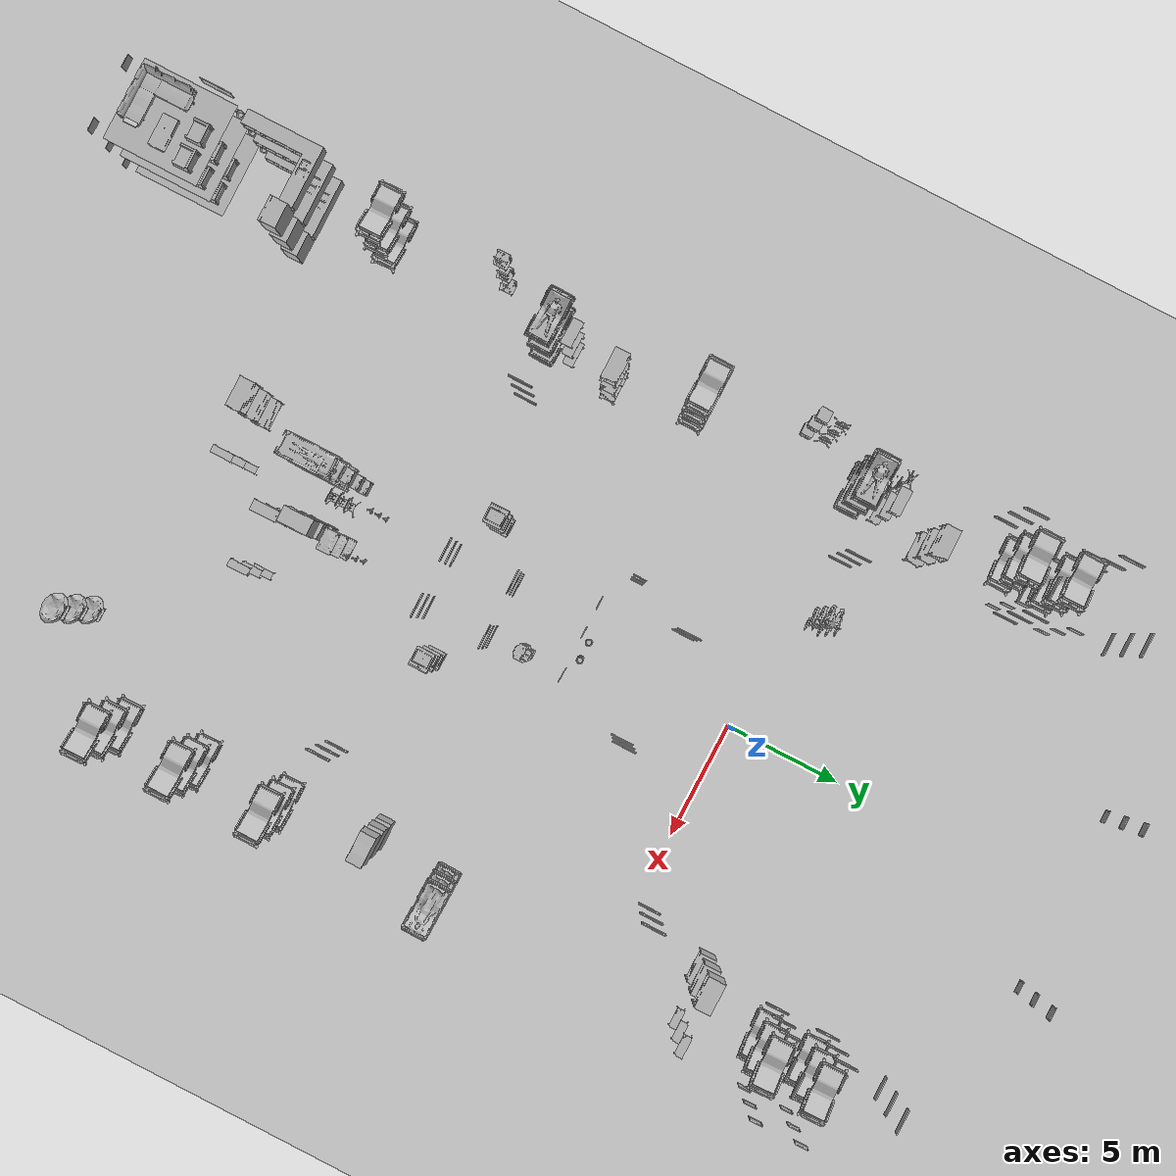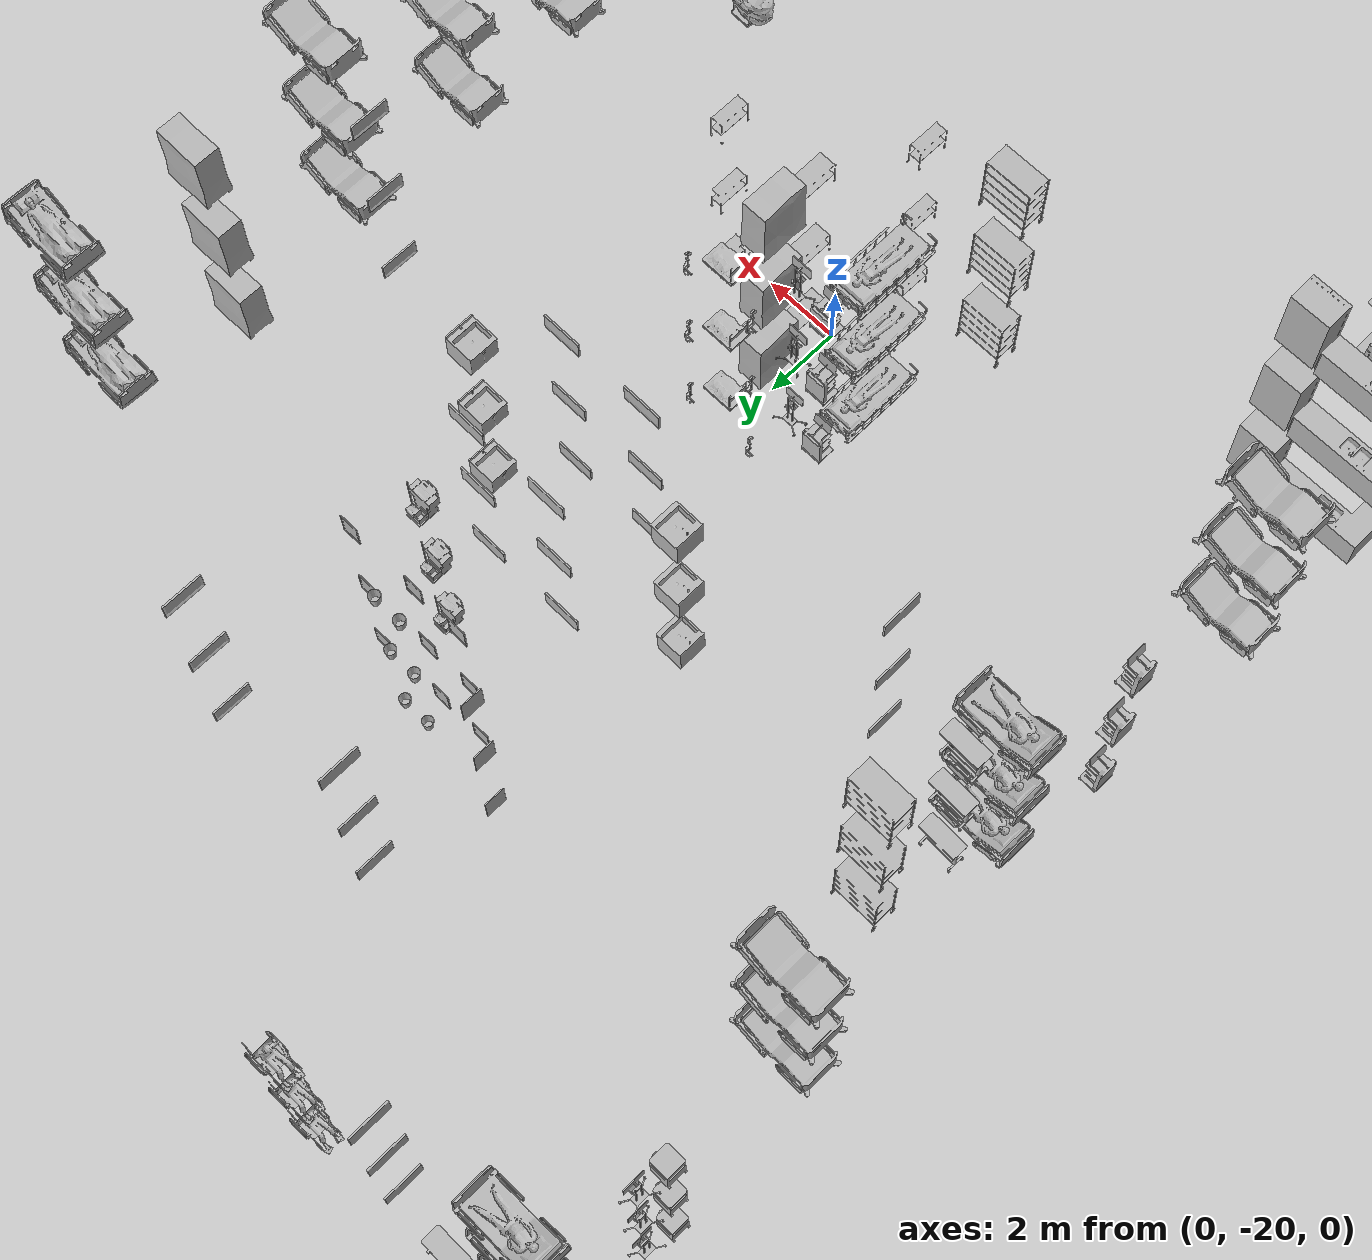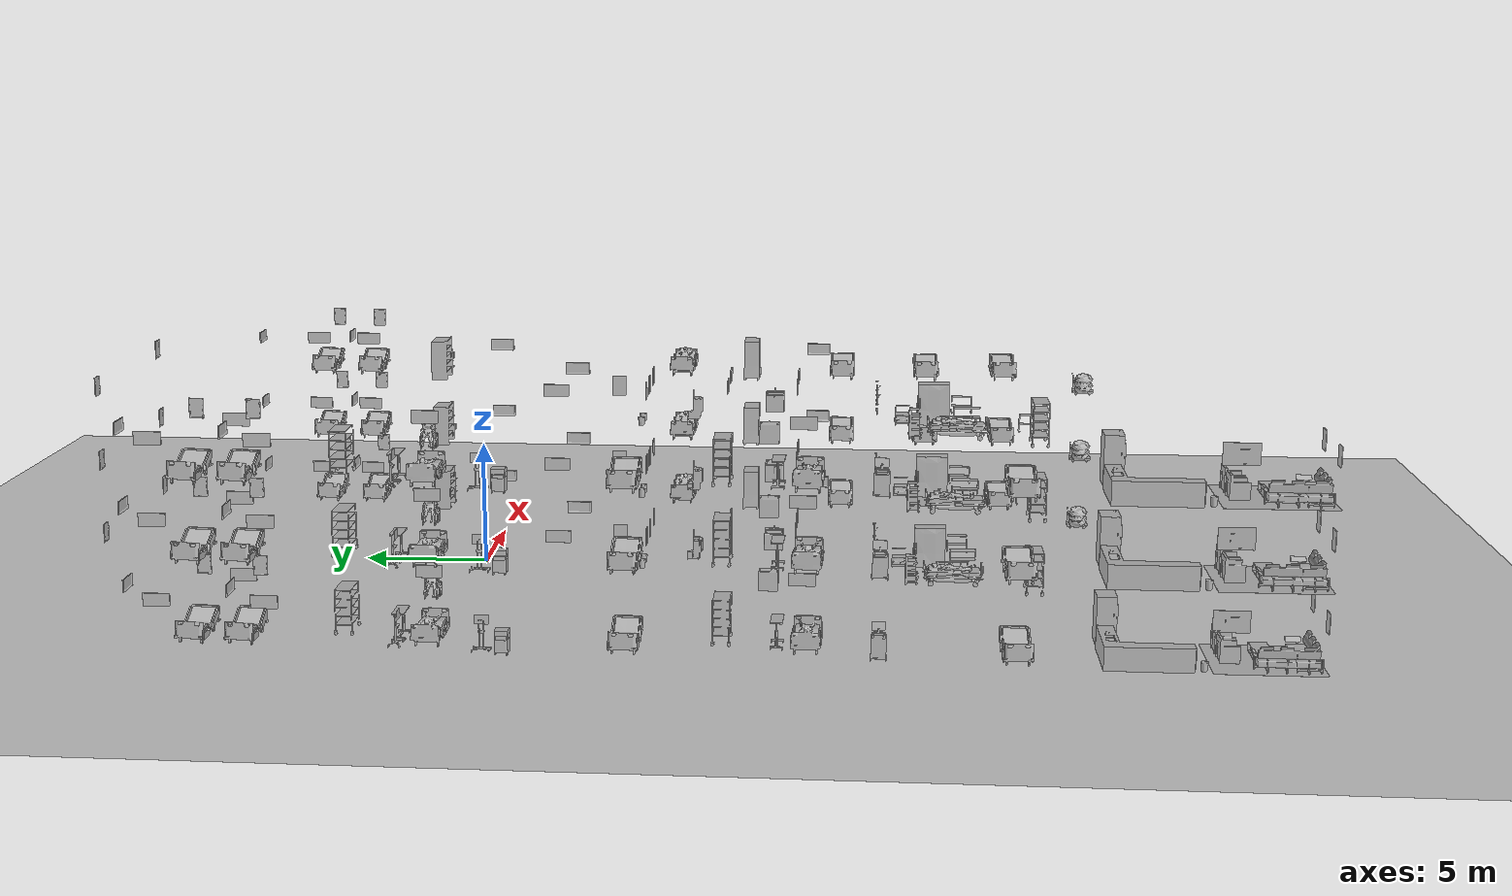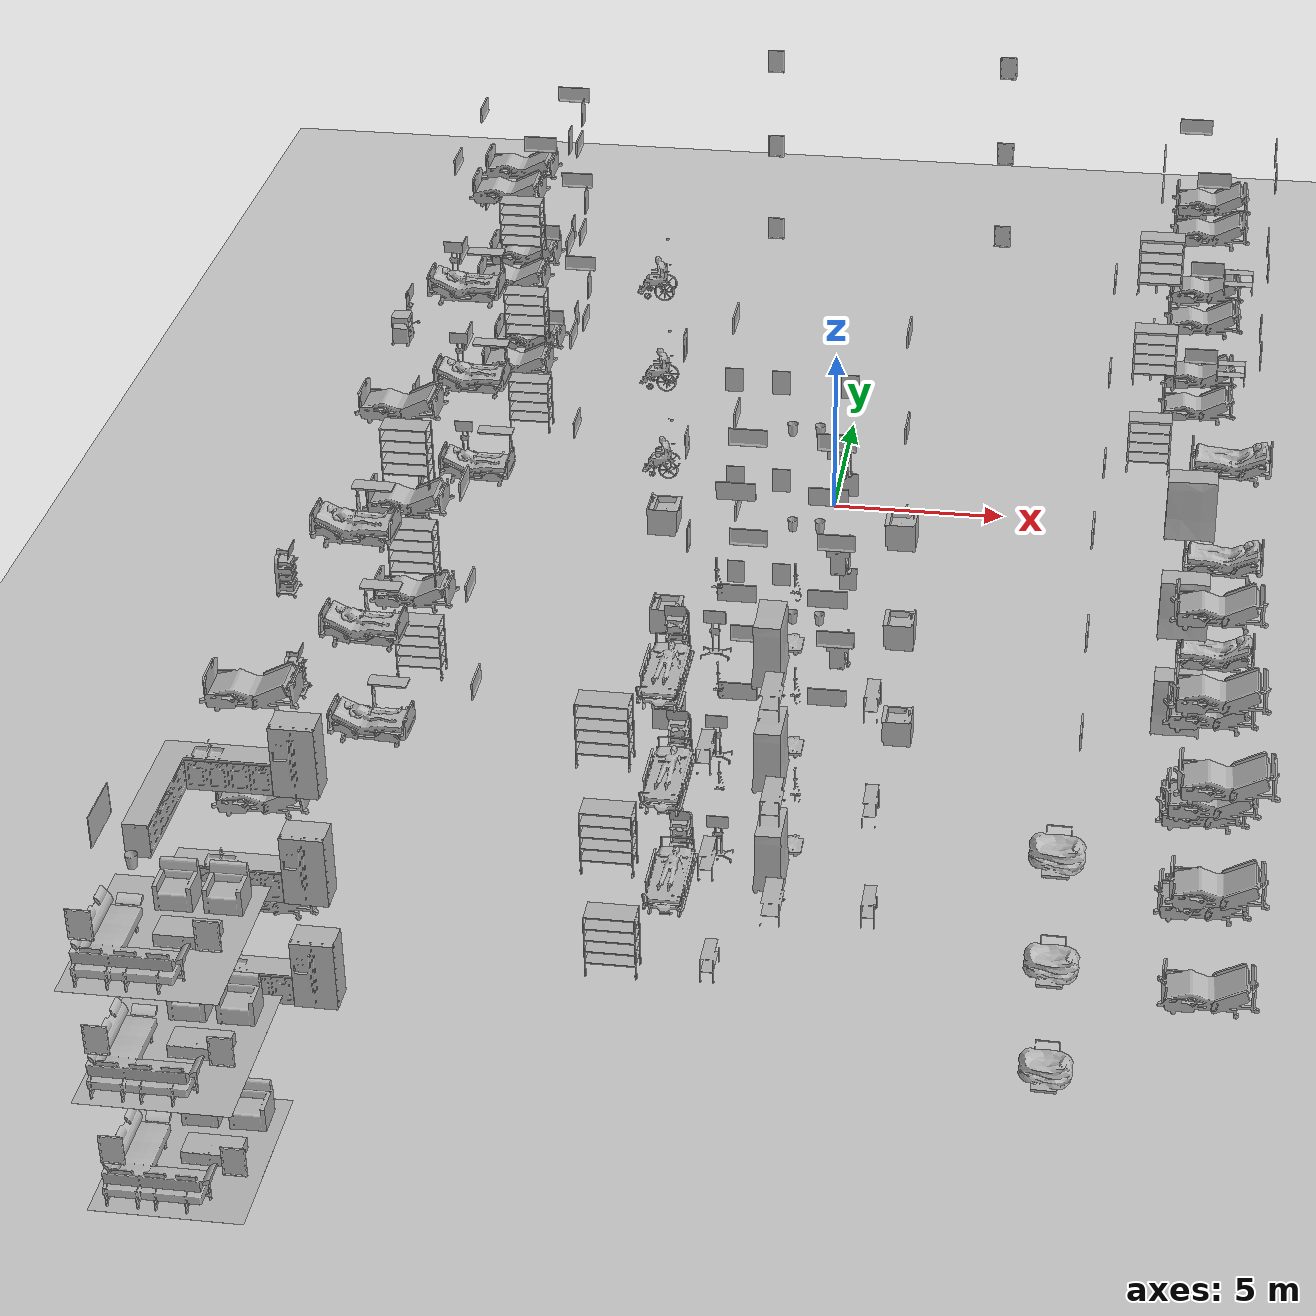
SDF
<sdf version="1.6">
 <world name="world">
  <gravity>0 0 -9.8</gravity>
  <physics default="0" name="default_physics" type="ode">
   <max_step_size>0.001</max_step_size>
   <real_time_factor>1</real_time_factor>
   <real_time_update_rate>1000</real_time_update_rate>
  </physics>
  <scene><ambient>0.6 0.6 0.6 1</ambient><background>0.4 0.4 0.4 1</background><shadows>false</shadows></scene>
  <plugin filename="gz-sim-physics-system" name="gz::sim::systems::Physics"/>
  <plugin filename="gz-sim-user-commands-system" name="gz::sim::systems::UserCommands"/>
  <plugin filename="gz-sim-scene-broadcaster-system" name="gz::sim::systems::SceneBroadcaster"/>
  <plugin filename="gz-sim-sensors-system" name="gz::sim::systems::Sensors">
   <render_engine>ogre2</render_engine>
  </plugin>
  <plugin filename="gz-sim-imu-system" name="gz::sim::systems::Imu"/>
  <plugin filename="gz-sim-contact-system" name="gz::sim::systems::Contact"/>
  <include><uri>model://sun</uri></include>
  <include><uri>model://ground_plane</uri><pose>0 0 -0.1 0 -0 0</pose></include>
  <include>
   <uri>model://CGMClassic</uri>
   <static>true</static>
   <name>CGMClassic_1</name>
   <pose>11.1777 -18.4129 0 0 0 -3.13719</pose>
  </include>
  <include>
   <uri>model://CGMClassic</uri>
   <static>true</static>
   <name>CGMClassic_2</name>
   <pose>11.1179 -14.6493 0 0 0 -3.13599</pose>
  </include>
  <include>
   <uri>model://PatientWheelChair</uri>
   <static>true</static>
   <name>PatientWheelChair_1</name>
   <pose>-5.46091 1.23577 0 0 0 -1.54828</pose>
  </include>
  <include>
   <uri>model://SurgicalTrolley</uri>
   <static>true</static>
   <name>SurgicalTrolley_1</name>
   <pose>11.4301 3.56328 0 0 -0 0</pose>
  </include>
  <include>
   <uri>model://CGMClassic</uri>
   <static>true</static>
   <name>CGMClassic_3</name>
   <pose>-11.2304 -21.1134 0 0 0 -3.11834</pose>
  </include>
  <include>
   <uri>model://aws_robomaker_residential_CoffeeTable_01</uri>
   <static>true</static>
   <name>aws_robomaker_residential_CoffeeTable_01_1</name>
   <pose>-10.2383 -29.9144 0 0 -0 0</pose>
  </include>
  <include>
   <uri>model://aws_robomaker_residential_Sofa_01</uri>
   <static>true</static>
   <name>aws_robomaker_residential_Sofa_01_1</name>
   <pose>-11.077 -30.5544 -1e-05 2.6e-05 -3e-06 1.56984</pose>
  </include>
  <include>
   <uri>model://aws_robomaker_residential_TV_02</uri>
   <static>true</static>
   <name>aws_robomaker_residential_TV_02_1</name>
   <pose>-12.4122 -28.4594 1.53211 0 -0 3.13999</pose>
  </include>
  <include>
   <uri>model://aws_robomaker_residential_KitchenCabinet_01</uri>
   <static>true</static>
   <name>aws_robomaker_residential_KitchenCabinet_01_1</name>
   <pose>-11.1379 -25.6941 0 0 -0 0</pose>
  </include>
  <include>
   <uri>model://aws_robomaker_residential_Refrigerator_01</uri>
   <static>true</static>
   <name>aws_robomaker_residential_Refrigerator_01_1</name>
   <pose>-9.28238 -24.5015 0 0 -0 0</pose>
  </include>
  <include>
   <uri>model://aws_robomaker_residential_SofaB_01</uri>
   <static>true</static>
   <name>aws_robomaker_residential_SofaB_01_1</name>
   <pose>-10.8238 -28.6662 -5e-06 -1.3e-05 -2e-06 -1.56116</pose>
  </include>
  <include>
   <uri>model://aws_robomaker_residential_SofaB_01</uri>
   <static>true</static>
   <name>aws_robomaker_residential_SofaB_01_2</name>
   <pose>-9.73697 -28.6538 -3e-06 1.3e-05 -4e-06 -1.56077</pose>
  </include>
  <include>
   <uri>model://aws_robomaker_residential_PortraitA_01</uri>
   <static>true</static>
   <name>aws_robomaker_residential_PortraitA_01_1</name>
   <pose>1.14738 -6.92303 1.41115 0 -0 0</pose>
  </include>
  <include>
   <uri>model://aws_robomaker_residential_PortraitD_02</uri>
   <static>true</static>
   <name>aws_robomaker_residential_PortraitD_02_1</name>
   <pose>2.40772 -3.61975 1.54508 0 0 -1.57619</pose>
  </include>
  <include>
   <uri>model://MopCart3</uri>
   <static>true</static>
   <name>MopCart3_1</name>
   <pose>1.07736 -8.59036 -6.7e-05 0 1e-06 0</pose>
  </include>
  <include>
   <uri>model://aws_robomaker_residential_PortraitA_01</uri>
   <static>true</static>
   <name>aws_robomaker_residential_PortraitA_01_2</name>
   <pose>-0.706092 -6.93108 1.41115 0 -0 0</pose>
  </include>
  <include>
   <uri>model://aws_robomaker_residential_PortraitA_01</uri>
   <static>true</static>
   <name>aws_robomaker_residential_PortraitA_01_3</name>
   <pose>-1.97245 -6.9216 1.41115 0 -0 0</pose>
  </include>
  <include>
   <uri>model://aws_robomaker_residential_PortraitD_02</uri>
   <static>true</static>
   <name>aws_robomaker_residential_PortraitD_02_2</name>
   <pose>-2.43341 -3.38621 1.54508 0 -0 1.57083</pose>
  </include>
  <include>
   <uri>model://ElderLadyPatient</uri>
   <static>true</static>
   <name>ElderLadyPatient_1</name>
   <pose>-10.9972 0.231354 0.001654 0 -0 0</pose>
  </include>
  <include>
   <uri>model://ElderLadyPatient</uri>
   <static>true</static>
   <name>ElderLadyPatient_2</name>
   <pose>-10.8133 -13.5925 0.001657 0 -2e-06 -0.025052</pose>
  </include>
  <include>
   <uri>model://CGMClassic</uri>
   <static>true</static>
   <name>CGMClassic_4</name>
   <pose>-11.0878 -7.00992 0 0 -0 3.1351</pose>
  </include>
  <include>
   <uri>model://aws_robomaker_residential_Trash_01</uri>
   <static>true</static>
   <name>aws_robomaker_residential_Trash_01_1</name>
   <pose>0.316178 -6.58235 0.000903 0 -2e-06 0</pose>
  </include>
  <include>
   <uri>model://aws_robomaker_residential_Trash_01</uri>
   <static>true</static>
   <name>aws_robomaker_residential_Trash_01_2</name>
   <pose>-0.436645 -6.57758 0.000903 -1e-06 -1e-06 0</pose>
  </include>
  <include>
   <uri>model://aws_robomaker_residential_Trash_01</uri>
   <static>true</static>
   <name>aws_robomaker_residential_Trash_01_3</name>
   <pose>-12.1773 -27.6293 0.000894 -1e-06 -1e-06 0</pose>
  </include>
  <include>
   <uri>model://aws_robomaker_residential_PortraitE_01</uri>
   <static>true</static>
   <name>aws_robomaker_residential_PortraitE_01_1</name>
   <pose>-9.06141 -31.9238 1.38136 0 -0 0</pose>
  </include>
  <include>
   <uri>model://aws_robomaker_residential_PortraitE_01</uri>
   <static>true</static>
   <name>aws_robomaker_residential_PortraitE_01_2</name>
   <pose>-11.7398 -31.9011 1.38136 0 -0 0</pose>
  </include>
  <include>
   <uri>model://InstrumentCart1</uri>
   <static>true</static>
   <name>InstrumentCart1_1</name>
   <pose>-11.8071 -16.1825 0 0 -0 1.56702</pose>
  </include>
  <include>
   <uri>model://InstrumentCart2</uri>
   <static>true</static>
   <name>InstrumentCart2_1</name>
   <pose>-12.0906 -1.87329 0.051875 0 -0 1.57773</pose>
  </include>
  <include>
   <uri>model://InstrumentCart2</uri>
   <static>true</static>
   <name>InstrumentCart2_2</name>
   <pose>-11.5231 1.34237 0 0 -0 0</pose>
  </include>
  <include>
   <uri>model://aws_robomaker_residential_Carpet_01</uri>
   <static>true</static>
   <name>aws_robomaker_residential_Carpet_01_1</name>
   <pose>-10.7338 -29.9243 0 0 -0 0</pose>
  </include>
  <include>
   <uri>model://CGMClassic</uri>
   <static>true</static>
   <name>CGMClassic_5</name>
   <pose>-11.0106 8.9505 -0.008203 -0.035019 -0.000392 3.13388</pose>
  </include>
  <include>
   <uri>model://CGMClassic</uri>
   <static>true</static>
   <name>CGMClassic_6</name>
   <pose>-11.025 7.10335 0 -0.035021 1.8e-05 -3.13762</pose>
  </include>
  <include>
   <uri>model://BedTable</uri>
   <static>true</static>
   <name>BedTable_1</name>
   <pose>-10.4759 1.39442 0.001184 0 -3e-06 0</pose>
  </include>
  <include>
   <uri>model://BedTable</uri>
   <static>true</static>
   <name>BedTable_2</name>
   <pose>-10.5874 -12.5084 0.001189 0 -0 3.11588</pose>
  </include>
  <include>
   <uri>model://BedsideTable</uri>
   <static>true</static>
   <name>BedsideTable_1</name>
   <pose>-12.1499 -2.63111 0.00018 1e-06 -0 -0.00878</pose>
  </include>
  <include>
   <uri>model://TrolleyBedPatient</uri>
   <static>true</static>
   <name>TrolleyBedPatient_1</name>
   <pose>-1.83202 -19.2612 0 0 -0 0</pose>
  </include>
  <include>
   <uri>model://Shower</uri>
   <static>true</static>
   <name>Shower_1</name>
   <pose>-1.07422 -16.1332 0 0 -0 0</pose>
  </include>
  <include>
   <uri>model://Shower</uri>
   <static>true</static>
   <name>Shower_2</name>
   <pose>0.853327 -16.1492 0 0 -0 0</pose>
  </include>
  <include>
   <uri>model://SurgicalTrolley</uri>
   <static>true</static>
   <name>SurgicalTrolley_2</name>
   <pose>-0.411421 -22.2085 0 0 0 -1.58175</pose>
  </include>
  <include>
   <uri>model://SurgicalTrolley</uri>
   <static>true</static>
   <name>SurgicalTrolley_3</name>
   <pose>3.11747 -19.6565 0 0 -0 1.57031</pose>
  </include>
  <include>
   <uri>model://SurgicalTrolleyMed</uri>
   <static>true</static>
   <name>SurgicalTrolleyMed_1</name>
   <pose>0.770804 -19.7749 0 0 0 -1.56798</pose>
  </include>
  <include>
   <uri>model://InstrumentCart1</uri>
   <static>true</static>
   <name>InstrumentCart1_2</name>
   <pose>-11.8071 -16.1825 0 0 -0 1.56702</pose>
  </include>
  <include>
   <uri>model://InstrumentCart2</uri>
   <static>true</static>
   <name>InstrumentCart2_3</name>
   <pose>-0.869537 -17.7436 0 0 0 -0.002595</pose>
  </include>
  <include>
   <uri>model://StorageRackCovered</uri>
   <static>true</static>
   <name>StorageRackCovered_1</name>
   <pose>0.546476 -18.3985 -0 0 -0 1.56584</pose>
  </include>
  <include>
   <uri>model://StorageRack</uri>
   <static>true</static>
   <name>StorageRack_2</name>
   <pose>-2.69866 -22.4178 -8e-06 0 4e-06 0</pose>
  </include>
  <include>
   <uri>model://KitchenSink</uri>
   <static>true</static>
   <name>KitchenSink_1</name>
   <pose>3.06236 -11.8809 -0.001614 0 -0 3.1391</pose>
  </include>
  <include>
   <uri>model://KitchenSink</uri>
   <static>true</static>
   <name>KitchenSink_2</name>
   <pose>-3.09305 -11.8988 -0.001609 0 -0 0</pose>
  </include>
  <include>
   <uri>model://aws_robomaker_residential_PortraitD_01</uri>
   <static>true</static>
   <name>aws_robomaker_residential_PortraitD_01_1</name>
   <pose>-1.14723 -10.143 1.57344 0 -0 0</pose>
  </include>
  <include>
   <uri>model://aws_robomaker_residential_PortraitD_01</uri>
   <static>true</static>
   <name>aws_robomaker_residential_PortraitD_01_2</name>
   <pose>1.16956 -10.1327 1.57344 0 -0 0</pose>
  </include>
  <include>
   <uri>model://aws_robomaker_residential_PortraitD_01</uri>
   <static>true</static>
   <name>aws_robomaker_residential_PortraitD_01_3</name>
   <pose>1.2703 -12.9084 1.57344 0 0 -3.14134</pose>
  </include>
  <include>
   <uri>model://aws_robomaker_residential_PortraitD_01</uri>
   <static>true</static>
   <name>aws_robomaker_residential_PortraitD_01_4</name>
   <pose>-1.06108 -12.9155 1.57344 0 0 -3.14134</pose>
  </include>
  <include>
   <uri>model://aws_robomaker_residential_PortraitD_02</uri>
   <static>true</static>
   <name>aws_robomaker_residential_PortraitD_02_3</name>
   <pose>7.89294 -13.6155 1.54508 0 0 -1.57619</pose>
  </include>
  <include>
   <uri>model://aws_robomaker_residential_PortraitD_02</uri>
   <static>true</static>
   <name>aws_robomaker_residential_PortraitD_02_4</name>
   <pose>7.88791 0.445446 1.54508 0 0 -1.57619</pose>
  </include>
  <include>
   <uri>model://aws_robomaker_residential_PortraitD_02</uri>
   <static>true</static>
   <name>aws_robomaker_residential_PortraitD_02_5</name>
   <pose>-7.92095 0.84255 1.54508 0 -0 1.57083</pose>
  </include>
  <include>
   <uri>model://aws_robomaker_residential_PortraitD_02</uri>
   <static>true</static>
   <name>aws_robomaker_residential_PortraitD_02_6</name>
   <pose>-7.90937 -13.3417 1.54508 0 -0 1.57083</pose>
  </include>
  <include>
   <uri>model://aws_robomaker_residential_PortraitD_02</uri>
   <static>true</static>
   <name>aws_robomaker_residential_PortraitD_02_7</name>
   <pose>-12.3841 6.01232 1.54508 0 -0 1.57083</pose>
  </include>
  <include>
   <uri>model://aws_robomaker_residential_PortraitD_02</uri>
   <static>true</static>
   <name>aws_robomaker_residential_PortraitD_02_8</name>
   <pose>-12.4276 9.98828 1.54508 0 -0 1.57083</pose>
  </include>
  <include>
   <uri>model://aws_robomaker_residential_PortraitE_02</uri>
   <static>true</static>
   <name>aws_robomaker_residential_PortraitE_02_1</name>
   <pose>-9.08927 9.19494 1.84129 0 0 -1.5625</pose>
  </include>
  <include>
   <uri>model://aws_robomaker_residential_PortraitD_02</uri>
   <static>true</static>
   <name>aws_robomaker_residential_PortraitD_02_9</name>
   <pose>-8.94468 7.73571 1.54508 0 -0 1.57083</pose>
  </include>
  <include>
   <uri>model://aws_robomaker_residential_PortraitE_02</uri>
   <static>true</static>
   <name>aws_robomaker_residential_PortraitE_02_2</name>
   <pose>-9.08305 7.04089 1.84129 0 0 -1.5625</pose>
  </include>
  <include>
   <uri>model://aws_robomaker_residential_PortraitD_01</uri>
   <static>true</static>
   <name>aws_robomaker_residential_PortraitD_01_5</name>
   <pose>-9.9148 11.9172 1.40573 0 -0 0</pose>
  </include>
  <include>
   <uri>model://aws_robomaker_residential_PortraitD_01</uri>
   <static>true</static>
   <name>aws_robomaker_residential_PortraitD_01_6</name>
   <pose>-10.2134 7.89752 1.40573 0 -0 0</pose>
  </include>
  <include>
   <uri>model://CGMClassic</uri>
   <static>true</static>
   <name>CGMClassic_7</name>
   <pose>10.6166 9.06291 -0.008203 -0.03501 0.000885 -3.11285</pose>
  </include>
  <include>
   <uri>model://CGMClassic</uri>
   <static>true</static>
   <name>CGMClassic_8</name>
   <pose>10.6006 6.90956 -0.008203 -0.035003 0.001133 -3.10576</pose>
  </include>
  <include>
   <uri>model://aws_robomaker_residential_PortraitD_02</uri>
   <static>true</static>
   <name>aws_robomaker_residential_PortraitD_02_10</name>
   <pose>9.06517 6.78742 1.54508 0 -0 1.57083</pose>
  </include>
  <include>
   <uri>model://aws_robomaker_residential_PortraitD_02</uri>
   <static>true</static>
   <name>aws_robomaker_residential_PortraitD_02_11</name>
   <pose>9.06517 9.05858 1.54508 0 -0 1.57083</pose>
  </include>
  <include>
   <uri>model://aws_robomaker_residential_PortraitE_02</uri>
   <static>true</static>
   <name>aws_robomaker_residential_PortraitE_02_3</name>
   <pose>12.3972 6.98849 1.84129 0 0 -1.5625</pose>
  </include>
  <include>
   <uri>model://aws_robomaker_residential_PortraitE_02</uri>
   <static>true</static>
   <name>aws_robomaker_residential_PortraitE_02_4</name>
   <pose>12.3972 8.87466 1.84129 0 0 -1.5625</pose>
  </include>
  <include>
   <uri>model://aws_robomaker_residential_PortraitE_02</uri>
   <static>true</static>
   <name>aws_robomaker_residential_PortraitE_02_5</name>
   <pose>-3.4385 -6.00525 1.84129 0 -0 1.56777</pose>
  </include>
  <include>
   <uri>model://aws_robomaker_residential_PortraitD_01</uri>
   <static>true</static>
   <name>aws_robomaker_residential_PortraitD_01_7</name>
   <pose>10.596 7.88308 1.40573 0 -0 0</pose>
  </include>
  <include>
   <uri>model://aws_robomaker_residential_PortraitD_01</uri>
   <static>true</static>
   <name>aws_robomaker_residential_PortraitD_01_8</name>
   <pose>9.98896 11.914 1.40573 0 -0 0</pose>
  </include>
  <include>
   <uri>model://ParkingTrolleyMin</uri>
   <static>true</static>
   <name>ParkingTrolleyMin_1</name>
   <pose>0.715846 -17.1496 -0.000121 -1e-06 -0 0</pose>
  </include>
  <include>
   <uri>model://MalePatientBed</uri>
   <static>true</static>
   <name>MalePatientBed_1</name>
   <pose>11.3771 -7.38891 0.001658 -1e-06 1e-06 3.11598</pose>
  </include>
  <include>
   <uri>model://CGMClassic</uri>
   <static>true</static>
   <name>CGMClassic_9</name>
   <pose>11.3613 -21.8867 0 0 0 -3.12292</pose>
  </include>
  <include>
   <uri>model://StorageRackCoverOpen</uri>
   <static>true</static>
   <name>StorageRackCoverOpen_1</name>
   <pose>9.15016 3.44263 -9e-06 1e-06 2e-06 0</pose>
  </include>
  <include>
   <uri>model://StorageRack</uri>
   <static>true</static>
   <name>StorageRack_3</name>
   <pose>-10.1178 -10.4694 -0 0 -0 0</pose>
  </include>
  <include>
   <uri>model://StorageRack</uri>
   <static>true</static>
   <name>StorageRack_4</name>
   <pose>-9.91557 3.5644 -9e-06 1e-06 1e-06 -0.000273</pose>
  </include>
  <include>
   <uri>model://StorageRackCovered</uri>
   <static>true</static>
   <name>StorageRackCovered_2</name>
   <pose>10.294 -10.577 -7e-06 3e-06 -0 3.13389</pose>
  </include>
  <include>
   <uri>model://InstrumentCart1</uri>
   <static>true</static>
   <name>InstrumentCart1_3</name>
   <pose>-1.83539 -17.5879 0 0 -0 0</pose>
  </include>
  <include>
   <uri>model://ParkingTrolleyMax</uri>
   <static>true</static>
   <name>ParkingTrolleyMax_1</name>
   <pose>7.71054 -25.1326 -0.000121 1e-06 -0 -1.59536</pose>
  </include>
  <include>
   <uri>model://aws_robomaker_residential_PortraitE_02</uri>
   <static>true</static>
   <name>aws_robomaker_residential_PortraitE_02_6</name>
   <pose>-3.74211 14.8725 1.54379 0 -0 0</pose>
  </include>
  <include>
   <uri>model://aws_robomaker_residential_PortraitE_01</uri>
   <static>true</static>
   <name>aws_robomaker_residential_PortraitE_01_3</name>
   <pose>3.85701 14.8779 1.69742 0 -0 0</pose>
  </include>
  <include>
   <uri>model://CGMClassic</uri>
   <static>true</static>
   <name>floor_1_CGMClassic_1</name>
   <pose>11.1777 -18.4129 3.0 0 0 -3.13719</pose>
  </include>
  <include>
   <uri>model://CGMClassic</uri>
   <static>true</static>
   <name>floor_1_CGMClassic_2</name>
   <pose>11.1179 -14.6493 3.0 0 0 -3.13599</pose>
  </include>
  <include>
   <uri>model://PatientWheelChair</uri>
   <static>true</static>
   <name>floor_1_PatientWheelChair_1</name>
   <pose>-5.46091 1.23577 3.0 0 0 -1.54828</pose>
  </include>
  <include>
   <uri>model://SurgicalTrolley</uri>
   <static>true</static>
   <name>floor_1_SurgicalTrolley_1</name>
   <pose>11.4301 3.56328 3.0 0 -0 0</pose>
  </include>
  <include>
   <uri>model://CGMClassic</uri>
   <static>true</static>
   <name>floor_1_CGMClassic_3</name>
   <pose>-11.2304 -21.1134 3.0 0 0 -3.11834</pose>
  </include>
  <include>
   <uri>model://aws_robomaker_residential_CoffeeTable_01</uri>
   <static>true</static>
   <name>floor_1_aws_robomaker_residential_CoffeeTable_01_1</name>
   <pose>-10.2383 -29.9144 3.0 0 -0 0</pose>
  </include>
  <include>
   <uri>model://aws_robomaker_residential_Sofa_01</uri>
   <static>true</static>
   <name>floor_1_aws_robomaker_residential_Sofa_01_1</name>
   <pose>-11.077 -30.5544 2.99999 2.6e-05 -3e-06 1.56984</pose>
  </include>
  <include>
   <uri>model://aws_robomaker_residential_TV_02</uri>
   <static>true</static>
   <name>floor_1_aws_robomaker_residential_TV_02_1</name>
   <pose>-12.4122 -28.4594 4.53211 0 -0 3.13999</pose>
  </include>
  <include>
   <uri>model://aws_robomaker_residential_KitchenCabinet_01</uri>
   <static>true</static>
   <name>floor_1_aws_robomaker_residential_KitchenCabinet_01_1</name>
   <pose>-11.1379 -25.6941 3.0 0 -0 0</pose>
  </include>
  <include>
   <uri>model://aws_robomaker_residential_Refrigerator_01</uri>
   <static>true</static>
   <name>floor_1_aws_robomaker_residential_Refrigerator_01_1</name>
   <pose>-9.28238 -24.5015 3.0 0 -0 0</pose>
  </include>
  <include>
   <uri>model://aws_robomaker_residential_SofaB_01</uri>
   <static>true</static>
   <name>floor_1_aws_robomaker_residential_SofaB_01_1</name>
   <pose>-10.8238 -28.6662 2.999995 -1.3e-05 -2e-06 -1.56116</pose>
  </include>
  <include>
   <uri>model://aws_robomaker_residential_SofaB_01</uri>
   <static>true</static>
   <name>floor_1_aws_robomaker_residential_SofaB_01_2</name>
   <pose>-9.73697 -28.6538 2.999997 1.3e-05 -4e-06 -1.56077</pose>
  </include>
  <include>
   <uri>model://aws_robomaker_residential_PortraitA_01</uri>
   <static>true</static>
   <name>floor_1_aws_robomaker_residential_PortraitA_01_1</name>
   <pose>1.14738 -6.92303 4.41115 0 -0 0</pose>
  </include>
  <include>
   <uri>model://aws_robomaker_residential_PortraitD_02</uri>
   <static>true</static>
   <name>floor_1_aws_robomaker_residential_PortraitD_02_1</name>
   <pose>2.40772 -3.61975 4.5450800000000005 0 0 -1.57619</pose>
  </include>
  <include>
   <uri>model://MopCart3</uri>
   <static>true</static>
   <name>floor_1_MopCart3_1</name>
   <pose>1.07736 -8.59036 2.999933 0 1e-06 0</pose>
  </include>
  <include>
   <uri>model://aws_robomaker_residential_PortraitA_01</uri>
   <static>true</static>
   <name>floor_1_aws_robomaker_residential_PortraitA_01_2</name>
   <pose>-0.706092 -6.93108 4.41115 0 -0 0</pose>
  </include>
  <include>
   <uri>model://aws_robomaker_residential_PortraitA_01</uri>
   <static>true</static>
   <name>floor_1_aws_robomaker_residential_PortraitA_01_3</name>
   <pose>-1.97245 -6.9216 4.41115 0 -0 0</pose>
  </include>
  <include>
   <uri>model://aws_robomaker_residential_PortraitD_02</uri>
   <static>true</static>
   <name>floor_1_aws_robomaker_residential_PortraitD_02_2</name>
   <pose>-2.43341 -3.38621 4.5450800000000005 0 -0 1.57083</pose>
  </include>
  <include>
   <uri>model://ElderLadyPatient</uri>
   <static>true</static>
   <name>floor_1_ElderLadyPatient_1</name>
   <pose>-10.9972 0.231354 3.001654 0 -0 0</pose>
  </include>
  <include>
   <uri>model://ElderLadyPatient</uri>
   <static>true</static>
   <name>floor_1_ElderLadyPatient_2</name>
   <pose>-10.8133 -13.5925 3.001657 0 -2e-06 -0.025052</pose>
  </include>
  <include>
   <uri>model://CGMClassic</uri>
   <static>true</static>
   <name>floor_1_CGMClassic_4</name>
   <pose>-11.0878 -7.00992 3.0 0 -0 3.1351</pose>
  </include>
  <include>
   <uri>model://aws_robomaker_residential_Trash_01</uri>
   <static>true</static>
   <name>floor_1_aws_robomaker_residential_Trash_01_1</name>
   <pose>0.316178 -6.58235 3.000903 0 -2e-06 0</pose>
  </include>
  <include>
   <uri>model://aws_robomaker_residential_Trash_01</uri>
   <static>true</static>
   <name>floor_1_aws_robomaker_residential_Trash_01_2</name>
   <pose>-0.436645 -6.57758 3.000903 -1e-06 -1e-06 0</pose>
  </include>
  <include>
   <uri>model://aws_robomaker_residential_Trash_01</uri>
   <static>true</static>
   <name>floor_1_aws_robomaker_residential_Trash_01_3</name>
   <pose>-12.1773 -27.6293 3.000894 -1e-06 -1e-06 0</pose>
  </include>
  <include>
   <uri>model://aws_robomaker_residential_PortraitE_01</uri>
   <static>true</static>
   <name>floor_1_aws_robomaker_residential_PortraitE_01_1</name>
   <pose>-9.06141 -31.9238 4.38136 0 -0 0</pose>
  </include>
  <include>
   <uri>model://aws_robomaker_residential_PortraitE_01</uri>
   <static>true</static>
   <name>floor_1_aws_robomaker_residential_PortraitE_01_2</name>
   <pose>-11.7398 -31.9011 4.38136 0 -0 0</pose>
  </include>
  <include>
   <uri>model://InstrumentCart1</uri>
   <static>true</static>
   <name>floor_1_InstrumentCart1_1</name>
   <pose>-11.8071 -16.1825 3.0 0 -0 1.56702</pose>
  </include>
  <include>
   <uri>model://InstrumentCart2</uri>
   <static>true</static>
   <name>floor_1_InstrumentCart2_1</name>
   <pose>-12.0906 -1.87329 3.051875 0 -0 1.57773</pose>
  </include>
  <include>
   <uri>model://InstrumentCart2</uri>
   <static>true</static>
   <name>floor_1_InstrumentCart2_2</name>
   <pose>-11.5231 1.34237 3.0 0 -0 0</pose>
  </include>
  <include>
   <uri>model://aws_robomaker_residential_Carpet_01</uri>
   <static>true</static>
   <name>floor_1_aws_robomaker_residential_Carpet_01_1</name>
   <pose>-10.7338 -29.9243 3.0 0 -0 0</pose>
  </include>
  <include>
   <uri>model://CGMClassic</uri>
   <static>true</static>
   <name>floor_1_CGMClassic_5</name>
   <pose>-11.0106 8.9505 2.991797 -0.035019 -0.000392 3.13388</pose>
  </include>
  <include>
   <uri>model://CGMClassic</uri>
   <static>true</static>
   <name>floor_1_CGMClassic_6</name>
   <pose>-11.025 7.10335 3.0 -0.035021 1.8e-05 -3.13762</pose>
  </include>
  <include>
   <uri>model://BedTable</uri>
   <static>true</static>
   <name>floor_1_BedTable_1</name>
   <pose>-10.4759 1.39442 3.001184 0 -3e-06 0</pose>
  </include>
  <include>
   <uri>model://BedTable</uri>
   <static>true</static>
   <name>floor_1_BedTable_2</name>
   <pose>-10.5874 -12.5084 3.001189 0 -0 3.11588</pose>
  </include>
  <include>
   <uri>model://BedsideTable</uri>
   <static>true</static>
   <name>floor_1_BedsideTable_1</name>
   <pose>-12.1499 -2.63111 3.00018 1e-06 -0 -0.00878</pose>
  </include>
  <include>
   <uri>model://TrolleyBedPatient</uri>
   <static>true</static>
   <name>floor_1_TrolleyBedPatient_1</name>
   <pose>-1.83202 -19.2612 3.0 0 -0 0</pose>
  </include>
  <include>
   <uri>model://Shower</uri>
   <static>true</static>
   <name>floor_1_Shower_1</name>
   <pose>-1.07422 -16.1332 3.0 0 -0 0</pose>
  </include>
  <include>
   <uri>model://Shower</uri>
   <static>true</static>
   <name>floor_1_Shower_2</name>
   <pose>0.853327 -16.1492 3.0 0 -0 0</pose>
  </include>
  <include>
   <uri>model://SurgicalTrolley</uri>
   <static>true</static>
   <name>floor_1_SurgicalTrolley_2</name>
   <pose>-0.411421 -22.2085 3.0 0 0 -1.58175</pose>
  </include>
  <include>
   <uri>model://SurgicalTrolley</uri>
   <static>true</static>
   <name>floor_1_SurgicalTrolley_3</name>
   <pose>3.11747 -19.6565 3.0 0 -0 1.57031</pose>
  </include>
  <include>
   <uri>model://SurgicalTrolleyMed</uri>
   <static>true</static>
   <name>floor_1_SurgicalTrolleyMed_1</name>
   <pose>0.770804 -19.7749 3.0 0 0 -1.56798</pose>
  </include>
  <include>
   <uri>model://InstrumentCart1</uri>
   <static>true</static>
   <name>floor_1_InstrumentCart1_2</name>
   <pose>-11.8071 -16.1825 3.0 0 -0 1.56702</pose>
  </include>
  <include>
   <uri>model://InstrumentCart2</uri>
   <static>true</static>
   <name>floor_1_InstrumentCart2_3</name>
   <pose>-0.869537 -17.7436 3.0 0 0 -0.002595</pose>
  </include>
  <include>
   <uri>model://StorageRackCovered</uri>
   <static>true</static>
   <name>floor_1_StorageRackCovered_1</name>
   <pose>0.546476 -18.3985 3.0 0 -0 1.56584</pose>
  </include>
  <include>
   <uri>model://StorageRack</uri>
   <static>true</static>
   <name>floor_1_StorageRack_2</name>
   <pose>-2.69866 -22.4178 2.999992 0 4e-06 0</pose>
  </include>
  <include>
   <uri>model://KitchenSink</uri>
   <static>true</static>
   <name>floor_1_KitchenSink_1</name>
   <pose>3.06236 -11.8809 2.998386 0 -0 3.1391</pose>
  </include>
  <include>
   <uri>model://KitchenSink</uri>
   <static>true</static>
   <name>floor_1_KitchenSink_2</name>
   <pose>-3.09305 -11.8988 2.998391 0 -0 0</pose>
  </include>
  <include>
   <uri>model://aws_robomaker_residential_PortraitD_01</uri>
   <static>true</static>
   <name>floor_1_aws_robomaker_residential_PortraitD_01_1</name>
   <pose>-1.14723 -10.143 4.57344 0 -0 0</pose>
  </include>
  <include>
   <uri>model://aws_robomaker_residential_PortraitD_01</uri>
   <static>true</static>
   <name>floor_1_aws_robomaker_residential_PortraitD_01_2</name>
   <pose>1.16956 -10.1327 4.57344 0 -0 0</pose>
  </include>
  <include>
   <uri>model://aws_robomaker_residential_PortraitD_01</uri>
   <static>true</static>
   <name>floor_1_aws_robomaker_residential_PortraitD_01_3</name>
   <pose>1.2703 -12.9084 4.57344 0 0 -3.14134</pose>
  </include>
  <include>
   <uri>model://aws_robomaker_residential_PortraitD_01</uri>
   <static>true</static>
   <name>floor_1_aws_robomaker_residential_PortraitD_01_4</name>
   <pose>-1.06108 -12.9155 4.57344 0 0 -3.14134</pose>
  </include>
  <include>
   <uri>model://aws_robomaker_residential_PortraitD_02</uri>
   <static>true</static>
   <name>floor_1_aws_robomaker_residential_PortraitD_02_3</name>
   <pose>7.89294 -13.6155 4.5450800000000005 0 0 -1.57619</pose>
  </include>
  <include>
   <uri>model://aws_robomaker_residential_PortraitD_02</uri>
   <static>true</static>
   <name>floor_1_aws_robomaker_residential_PortraitD_02_4</name>
   <pose>7.88791 0.445446 4.5450800000000005 0 0 -1.57619</pose>
  </include>
  <include>
   <uri>model://aws_robomaker_residential_PortraitD_02</uri>
   <static>true</static>
   <name>floor_1_aws_robomaker_residential_PortraitD_02_5</name>
   <pose>-7.92095 0.84255 4.5450800000000005 0 -0 1.57083</pose>
  </include>
  <include>
   <uri>model://aws_robomaker_residential_PortraitD_02</uri>
   <static>true</static>
   <name>floor_1_aws_robomaker_residential_PortraitD_02_6</name>
   <pose>-7.90937 -13.3417 4.5450800000000005 0 -0 1.57083</pose>
  </include>
  <include>
   <uri>model://aws_robomaker_residential_PortraitD_02</uri>
   <static>true</static>
   <name>floor_1_aws_robomaker_residential_PortraitD_02_7</name>
   <pose>-12.3841 6.01232 4.5450800000000005 0 -0 1.57083</pose>
  </include>
  <include>
   <uri>model://aws_robomaker_residential_PortraitD_02</uri>
   <static>true</static>
   <name>floor_1_aws_robomaker_residential_PortraitD_02_8</name>
   <pose>-12.4276 9.98828 4.5450800000000005 0 -0 1.57083</pose>
  </include>
  <include>
   <uri>model://aws_robomaker_residential_PortraitE_02</uri>
   <static>true</static>
   <name>floor_1_aws_robomaker_residential_PortraitE_02_1</name>
   <pose>-9.08927 9.19494 4.84129 0 0 -1.5625</pose>
  </include>
  <include>
   <uri>model://aws_robomaker_residential_PortraitD_02</uri>
   <static>true</static>
   <name>floor_1_aws_robomaker_residential_PortraitD_02_9</name>
   <pose>-8.94468 7.73571 4.5450800000000005 0 -0 1.57083</pose>
  </include>
  <include>
   <uri>model://aws_robomaker_residential_PortraitE_02</uri>
   <static>true</static>
   <name>floor_1_aws_robomaker_residential_PortraitE_02_2</name>
   <pose>-9.08305 7.04089 4.84129 0 0 -1.5625</pose>
  </include>
  <include>
   <uri>model://aws_robomaker_residential_PortraitD_01</uri>
   <static>true</static>
   <name>floor_1_aws_robomaker_residential_PortraitD_01_5</name>
   <pose>-9.9148 11.9172 4.40573 0 -0 0</pose>
  </include>
  <include>
   <uri>model://aws_robomaker_residential_PortraitD_01</uri>
   <static>true</static>
   <name>floor_1_aws_robomaker_residential_PortraitD_01_6</name>
   <pose>-10.2134 7.89752 4.40573 0 -0 0</pose>
  </include>
  <include>
   <uri>model://CGMClassic</uri>
   <static>true</static>
   <name>floor_1_CGMClassic_7</name>
   <pose>10.6166 9.06291 2.991797 -0.03501 0.000885 -3.11285</pose>
  </include>
  <include>
   <uri>model://CGMClassic</uri>
   <static>true</static>
   <name>floor_1_CGMClassic_8</name>
   <pose>10.6006 6.90956 2.991797 -0.035003 0.001133 -3.10576</pose>
  </include>
  <include>
   <uri>model://aws_robomaker_residential_PortraitD_02</uri>
   <static>true</static>
   <name>floor_1_aws_robomaker_residential_PortraitD_02_10</name>
   <pose>9.06517 6.78742 4.5450800000000005 0 -0 1.57083</pose>
  </include>
  <include>
   <uri>model://aws_robomaker_residential_PortraitD_02</uri>
   <static>true</static>
   <name>floor_1_aws_robomaker_residential_PortraitD_02_11</name>
   <pose>9.06517 9.05858 4.5450800000000005 0 -0 1.57083</pose>
  </include>
  <include>
   <uri>model://aws_robomaker_residential_PortraitE_02</uri>
   <static>true</static>
   <name>floor_1_aws_robomaker_residential_PortraitE_02_3</name>
   <pose>12.3972 6.98849 4.84129 0 0 -1.5625</pose>
  </include>
  <include>
   <uri>model://aws_robomaker_residential_PortraitE_02</uri>
   <static>true</static>
   <name>floor_1_aws_robomaker_residential_PortraitE_02_4</name>
   <pose>12.3972 8.87466 4.84129 0 0 -1.5625</pose>
  </include>
  <include>
   <uri>model://aws_robomaker_residential_PortraitE_02</uri>
   <static>true</static>
   <name>floor_1_aws_robomaker_residential_PortraitE_02_5</name>
   <pose>-3.4385 -6.00525 4.84129 0 -0 1.56777</pose>
  </include>
  <include>
   <uri>model://aws_robomaker_residential_PortraitD_01</uri>
   <static>true</static>
   <name>floor_1_aws_robomaker_residential_PortraitD_01_7</name>
   <pose>10.596 7.88308 4.40573 0 -0 0</pose>
  </include>
  <include>
   <uri>model://aws_robomaker_residential_PortraitD_01</uri>
   <static>true</static>
   <name>floor_1_aws_robomaker_residential_PortraitD_01_8</name>
   <pose>9.98896 11.914 4.40573 0 -0 0</pose>
  </include>
  <include>
   <uri>model://ParkingTrolleyMin</uri>
   <static>true</static>
   <name>floor_1_ParkingTrolleyMin_1</name>
   <pose>0.715846 -17.1496 2.999879 -1e-06 -0 0</pose>
  </include>
  <include>
   <uri>model://MalePatientBed</uri>
   <static>true</static>
   <name>floor_1_MalePatientBed_1</name>
   <pose>11.3771 -7.38891 3.001658 -1e-06 1e-06 3.11598</pose>
  </include>
  <include>
   <uri>model://CGMClassic</uri>
   <static>true</static>
   <name>floor_1_CGMClassic_9</name>
   <pose>11.3613 -21.8867 3.0 0 0 -3.12292</pose>
  </include>
  <include>
   <uri>model://StorageRackCoverOpen</uri>
   <static>true</static>
   <name>floor_1_StorageRackCoverOpen_1</name>
   <pose>9.15016 3.44263 2.999991 1e-06 2e-06 0</pose>
  </include>
  <include>
   <uri>model://StorageRack</uri>
   <static>true</static>
   <name>floor_1_StorageRack_3</name>
   <pose>-10.1178 -10.4694 3.0 0 -0 0</pose>
  </include>
  <include>
   <uri>model://StorageRack</uri>
   <static>true</static>
   <name>floor_1_StorageRack_4</name>
   <pose>-9.91557 3.5644 2.999991 1e-06 1e-06 -0.000273</pose>
  </include>
  <include>
   <uri>model://StorageRackCovered</uri>
   <static>true</static>
   <name>floor_1_StorageRackCovered_2</name>
   <pose>10.294 -10.577 2.999993 3e-06 -0 3.13389</pose>
  </include>
  <include>
   <uri>model://InstrumentCart1</uri>
   <static>true</static>
   <name>floor_1_InstrumentCart1_3</name>
   <pose>-1.83539 -17.5879 3.0 0 -0 0</pose>
  </include>
  <include>
   <uri>model://ParkingTrolleyMax</uri>
   <static>true</static>
   <name>floor_1_ParkingTrolleyMax_1</name>
   <pose>7.71054 -25.1326 2.999879 1e-06 -0 -1.59536</pose>
  </include>
  <include>
   <uri>model://aws_robomaker_residential_PortraitE_02</uri>
   <static>true</static>
   <name>floor_1_aws_robomaker_residential_PortraitE_02_6</name>
   <pose>-3.74211 14.8725 4.5437899999999996 0 -0 0</pose>
  </include>
  <include>
   <uri>model://aws_robomaker_residential_PortraitE_01</uri>
   <static>true</static>
   <name>floor_1_aws_robomaker_residential_PortraitE_01_3</name>
   <pose>3.85701 14.8779 4.69742 0 -0 0</pose>
  </include>
  <include>
   <uri>model://CGMClassic</uri>
   <static>true</static>
   <name>floor_2_CGMClassic_1</name>
   <pose>11.1777 -18.4129 6.0 0 0 -3.13719</pose>
  </include>
  <include>
   <uri>model://CGMClassic</uri>
   <static>true</static>
   <name>floor_2_CGMClassic_2</name>
   <pose>11.1179 -14.6493 6.0 0 0 -3.13599</pose>
  </include>
  <include>
   <uri>model://PatientWheelChair</uri>
   <static>true</static>
   <name>floor_2_PatientWheelChair_1</name>
   <pose>-5.46091 1.23577 6.0 0 0 -1.54828</pose>
  </include>
  <include>
   <uri>model://SurgicalTrolley</uri>
   <static>true</static>
   <name>floor_2_SurgicalTrolley_1</name>
   <pose>11.4301 3.56328 6.0 0 -0 0</pose>
  </include>
  <include>
   <uri>model://CGMClassic</uri>
   <static>true</static>
   <name>floor_2_CGMClassic_3</name>
   <pose>-11.2304 -21.1134 6.0 0 0 -3.11834</pose>
  </include>
  <include>
   <uri>model://aws_robomaker_residential_CoffeeTable_01</uri>
   <static>true</static>
   <name>floor_2_aws_robomaker_residential_CoffeeTable_01_1</name>
   <pose>-10.2383 -29.9144 6.0 0 -0 0</pose>
  </include>
  <include>
   <uri>model://aws_robomaker_residential_Sofa_01</uri>
   <static>true</static>
   <name>floor_2_aws_robomaker_residential_Sofa_01_1</name>
   <pose>-11.077 -30.5544 5.99999 2.6e-05 -3e-06 1.56984</pose>
  </include>
  <include>
   <uri>model://aws_robomaker_residential_TV_02</uri>
   <static>true</static>
   <name>floor_2_aws_robomaker_residential_TV_02_1</name>
   <pose>-12.4122 -28.4594 7.53211 0 -0 3.13999</pose>
  </include>
  <include>
   <uri>model://aws_robomaker_residential_KitchenCabinet_01</uri>
   <static>true</static>
   <name>floor_2_aws_robomaker_residential_KitchenCabinet_01_1</name>
   <pose>-11.1379 -25.6941 6.0 0 -0 0</pose>
  </include>
  <include>
   <uri>model://aws_robomaker_residential_Refrigerator_01</uri>
   <static>true</static>
   <name>floor_2_aws_robomaker_residential_Refrigerator_01_1</name>
   <pose>-9.28238 -24.5015 6.0 0 -0 0</pose>
  </include>
  <include>
   <uri>model://aws_robomaker_residential_SofaB_01</uri>
   <static>true</static>
   <name>floor_2_aws_robomaker_residential_SofaB_01_1</name>
   <pose>-10.8238 -28.6662 5.999995 -1.3e-05 -2e-06 -1.56116</pose>
  </include>
  <include>
   <uri>model://aws_robomaker_residential_SofaB_01</uri>
   <static>true</static>
   <name>floor_2_aws_robomaker_residential_SofaB_01_2</name>
   <pose>-9.73697 -28.6538 5.999997 1.3e-05 -4e-06 -1.56077</pose>
  </include>
  <include>
   <uri>model://aws_robomaker_residential_PortraitA_01</uri>
   <static>true</static>
   <name>floor_2_aws_robomaker_residential_PortraitA_01_1</name>
   <pose>1.14738 -6.92303 7.41115 0 -0 0</pose>
  </include>
  <include>
   <uri>model://aws_robomaker_residential_PortraitD_02</uri>
   <static>true</static>
   <name>floor_2_aws_robomaker_residential_PortraitD_02_1</name>
   <pose>2.40772 -3.61975 7.5450800000000005 0 0 -1.57619</pose>
  </include>
  <include>
   <uri>model://MopCart3</uri>
   <static>true</static>
   <name>floor_2_MopCart3_1</name>
   <pose>1.07736 -8.59036 5.999933 0 1e-06 0</pose>
  </include>
  <include>
   <uri>model://aws_robomaker_residential_PortraitA_01</uri>
   <static>true</static>
   <name>floor_2_aws_robomaker_residential_PortraitA_01_2</name>
   <pose>-0.706092 -6.93108 7.41115 0 -0 0</pose>
  </include>
  <include>
   <uri>model://aws_robomaker_residential_PortraitA_01</uri>
   <static>true</static>
   <name>floor_2_aws_robomaker_residential_PortraitA_01_3</name>
   <pose>-1.97245 -6.9216 7.41115 0 -0 0</pose>
  </include>
  <include>
   <uri>model://aws_robomaker_residential_PortraitD_02</uri>
   <static>true</static>
   <name>floor_2_aws_robomaker_residential_PortraitD_02_2</name>
   <pose>-2.43341 -3.38621 7.5450800000000005 0 -0 1.57083</pose>
  </include>
  <include>
   <uri>model://ElderLadyPatient</uri>
   <static>true</static>
   <name>floor_2_ElderLadyPatient_1</name>
   <pose>-10.9972 0.231354 6.001654 0 -0 0</pose>
  </include>
  <include>
   <uri>model://ElderLadyPatient</uri>
   <static>true</static>
   <name>floor_2_ElderLadyPatient_2</name>
   <pose>-10.8133 -13.5925 6.001657 0 -2e-06 -0.025052</pose>
  </include>
  <include>
   <uri>model://CGMClassic</uri>
   <static>true</static>
   <name>floor_2_CGMClassic_4</name>
   <pose>-11.0878 -7.00992 6.0 0 -0 3.1351</pose>
  </include>
  <include>
   <uri>model://aws_robomaker_residential_Trash_01</uri>
   <static>true</static>
   <name>floor_2_aws_robomaker_residential_Trash_01_1</name>
   <pose>0.316178 -6.58235 6.000903 0 -2e-06 0</pose>
  </include>
  <include>
   <uri>model://aws_robomaker_residential_Trash_01</uri>
   <static>true</static>
   <name>floor_2_aws_robomaker_residential_Trash_01_2</name>
   <pose>-0.436645 -6.57758 6.000903 -1e-06 -1e-06 0</pose>
  </include>
  <include>
   <uri>model://aws_robomaker_residential_Trash_01</uri>
   <static>true</static>
   <name>floor_2_aws_robomaker_residential_Trash_01_3</name>
   <pose>-12.1773 -27.6293 6.000894 -1e-06 -1e-06 0</pose>
  </include>
  <include>
   <uri>model://aws_robomaker_residential_PortraitE_01</uri>
   <static>true</static>
   <name>floor_2_aws_robomaker_residential_PortraitE_01_1</name>
   <pose>-9.06141 -31.9238 7.38136 0 -0 0</pose>
  </include>
  <include>
   <uri>model://aws_robomaker_residential_PortraitE_01</uri>
   <static>true</static>
   <name>floor_2_aws_robomaker_residential_PortraitE_01_2</name>
   <pose>-11.7398 -31.9011 7.38136 0 -0 0</pose>
  </include>
  <include>
   <uri>model://InstrumentCart1</uri>
   <static>true</static>
   <name>floor_2_InstrumentCart1_1</name>
   <pose>-11.8071 -16.1825 6.0 0 -0 1.56702</pose>
  </include>
  <include>
   <uri>model://InstrumentCart2</uri>
   <static>true</static>
   <name>floor_2_InstrumentCart2_1</name>
   <pose>-12.0906 -1.87329 6.051875 0 -0 1.57773</pose>
  </include>
  <include>
   <uri>model://InstrumentCart2</uri>
   <static>true</static>
   <name>floor_2_InstrumentCart2_2</name>
   <pose>-11.5231 1.34237 6.0 0 -0 0</pose>
  </include>
  <include>
   <uri>model://aws_robomaker_residential_Carpet_01</uri>
   <static>true</static>
   <name>floor_2_aws_robomaker_residential_Carpet_01_1</name>
   <pose>-10.7338 -29.9243 6.0 0 -0 0</pose>
  </include>
  <include>
   <uri>model://CGMClassic</uri>
   <static>true</static>
   <name>floor_2_CGMClassic_5</name>
   <pose>-11.0106 8.9505 5.991797 -0.035019 -0.000392 3.13388</pose>
  </include>
  <include>
   <uri>model://CGMClassic</uri>
   <static>true</static>
   <name>floor_2_CGMClassic_6</name>
   <pose>-11.025 7.10335 6.0 -0.035021 1.8e-05 -3.13762</pose>
  </include>
  <include>
   <uri>model://BedTable</uri>
   <static>true</static>
   <name>floor_2_BedTable_1</name>
   <pose>-10.4759 1.39442 6.001184 0 -3e-06 0</pose>
  </include>
  <include>
   <uri>model://BedTable</uri>
   <static>true</static>
   <name>floor_2_BedTable_2</name>
   <pose>-10.5874 -12.5084 6.001189 0 -0 3.11588</pose>
  </include>
  <include>
   <uri>model://BedsideTable</uri>
   <static>true</static>
   <name>floor_2_BedsideTable_1</name>
   <pose>-12.1499 -2.63111 6.00018 1e-06 -0 -0.00878</pose>
  </include>
  <include>
   <uri>model://TrolleyBedPatient</uri>
   <static>true</static>
   <name>floor_2_TrolleyBedPatient_1</name>
   <pose>-1.83202 -19.2612 6.0 0 -0 0</pose>
  </include>
  <include>
   <uri>model://Shower</uri>
   <static>true</static>
   <name>floor_2_Shower_1</name>
   <pose>-1.07422 -16.1332 6.0 0 -0 0</pose>
  </include>
  <include>
   <uri>model://Shower</uri>
   <static>true</static>
   <name>floor_2_Shower_2</name>
   <pose>0.853327 -16.1492 6.0 0 -0 0</pose>
  </include>
  <include>
   <uri>model://SurgicalTrolley</uri>
   <static>true</static>
   <name>floor_2_SurgicalTrolley_2</name>
   <pose>-0.411421 -22.2085 6.0 0 0 -1.58175</pose>
  </include>
  <include>
   <uri>model://SurgicalTrolley</uri>
   <static>true</static>
   <name>floor_2_SurgicalTrolley_3</name>
   <pose>3.11747 -19.6565 6.0 0 -0 1.57031</pose>
  </include>
  <include>
   <uri>model://SurgicalTrolleyMed</uri>
   <static>true</static>
   <name>floor_2_SurgicalTrolleyMed_1</name>
   <pose>0.770804 -19.7749 6.0 0 0 -1.56798</pose>
  </include>
  <include>
   <uri>model://InstrumentCart1</uri>
   <static>true</static>
   <name>floor_2_InstrumentCart1_2</name>
   <pose>-11.8071 -16.1825 6.0 0 -0 1.56702</pose>
  </include>
  <include>
   <uri>model://InstrumentCart2</uri>
   <static>true</static>
   <name>floor_2_InstrumentCart2_3</name>
   <pose>-0.869537 -17.7436 6.0 0 0 -0.002595</pose>
  </include>
  <include>
   <uri>model://StorageRackCovered</uri>
   <static>true</static>
   <name>floor_2_StorageRackCovered_1</name>
   <pose>0.546476 -18.3985 6.0 0 -0 1.56584</pose>
  </include>
  <include>
   <uri>model://StorageRack</uri>
   <static>true</static>
   <name>floor_2_StorageRack_2</name>
   <pose>-2.69866 -22.4178 5.999992 0 4e-06 0</pose>
  </include>
  <include>
   <uri>model://KitchenSink</uri>
   <static>true</static>
   <name>floor_2_KitchenSink_1</name>
   <pose>3.06236 -11.8809 5.998386 0 -0 3.1391</pose>
  </include>
  <include>
   <uri>model://KitchenSink</uri>
   <static>true</static>
   <name>floor_2_KitchenSink_2</name>
   <pose>-3.09305 -11.8988 5.998391 0 -0 0</pose>
  </include>
  <include>
   <uri>model://aws_robomaker_residential_PortraitD_01</uri>
   <static>true</static>
   <name>floor_2_aws_robomaker_residential_PortraitD_01_1</name>
   <pose>-1.14723 -10.143 7.57344 0 -0 0</pose>
  </include>
  <include>
   <uri>model://aws_robomaker_residential_PortraitD_01</uri>
   <static>true</static>
   <name>floor_2_aws_robomaker_residential_PortraitD_01_2</name>
   <pose>1.16956 -10.1327 7.57344 0 -0 0</pose>
  </include>
  <include>
   <uri>model://aws_robomaker_residential_PortraitD_01</uri>
   <static>true</static>
   <name>floor_2_aws_robomaker_residential_PortraitD_01_3</name>
   <pose>1.2703 -12.9084 7.57344 0 0 -3.14134</pose>
  </include>
  <include>
   <uri>model://aws_robomaker_residential_PortraitD_01</uri>
   <static>true</static>
   <name>floor_2_aws_robomaker_residential_PortraitD_01_4</name>
   <pose>-1.06108 -12.9155 7.57344 0 0 -3.14134</pose>
  </include>
  <include>
   <uri>model://aws_robomaker_residential_PortraitD_02</uri>
   <static>true</static>
   <name>floor_2_aws_robomaker_residential_PortraitD_02_3</name>
   <pose>7.89294 -13.6155 7.5450800000000005 0 0 -1.57619</pose>
  </include>
  <include>
   <uri>model://aws_robomaker_residential_PortraitD_02</uri>
   <static>true</static>
   <name>floor_2_aws_robomaker_residential_PortraitD_02_4</name>
   <pose>7.88791 0.445446 7.5450800000000005 0 0 -1.57619</pose>
  </include>
  <include>
   <uri>model://aws_robomaker_residential_PortraitD_02</uri>
   <static>true</static>
   <name>floor_2_aws_robomaker_residential_PortraitD_02_5</name>
   <pose>-7.92095 0.84255 7.5450800000000005 0 -0 1.57083</pose>
  </include>
  <include>
   <uri>model://aws_robomaker_residential_PortraitD_02</uri>
   <static>true</static>
   <name>floor_2_aws_robomaker_residential_PortraitD_02_6</name>
   <pose>-7.90937 -13.3417 7.5450800000000005 0 -0 1.57083</pose>
  </include>
  <include>
   <uri>model://aws_robomaker_residential_PortraitD_02</uri>
   <static>true</static>
   <name>floor_2_aws_robomaker_residential_PortraitD_02_7</name>
   <pose>-12.3841 6.01232 7.5450800000000005 0 -0 1.57083</pose>
  </include>
  <include>
   <uri>model://aws_robomaker_residential_PortraitD_02</uri>
   <static>true</static>
   <name>floor_2_aws_robomaker_residential_PortraitD_02_8</name>
   <pose>-12.4276 9.98828 7.5450800000000005 0 -0 1.57083</pose>
  </include>
  <include>
   <uri>model://aws_robomaker_residential_PortraitE_02</uri>
   <static>true</static>
   <name>floor_2_aws_robomaker_residential_PortraitE_02_1</name>
   <pose>-9.08927 9.19494 7.84129 0 0 -1.5625</pose>
  </include>
  <include>
   <uri>model://aws_robomaker_residential_PortraitD_02</uri>
   <static>true</static>
   <name>floor_2_aws_robomaker_residential_PortraitD_02_9</name>
   <pose>-8.94468 7.73571 7.5450800000000005 0 -0 1.57083</pose>
  </include>
  <include>
   <uri>model://aws_robomaker_residential_PortraitE_02</uri>
   <static>true</static>
   <name>floor_2_aws_robomaker_residential_PortraitE_02_2</name>
   <pose>-9.08305 7.04089 7.84129 0 0 -1.5625</pose>
  </include>
  <include>
   <uri>model://aws_robomaker_residential_PortraitD_01</uri>
   <static>true</static>
   <name>floor_2_aws_robomaker_residential_PortraitD_01_5</name>
   <pose>-9.9148 11.9172 7.40573 0 -0 0</pose>
  </include>
  <include>
   <uri>model://aws_robomaker_residential_PortraitD_01</uri>
   <static>true</static>
   <name>floor_2_aws_robomaker_residential_PortraitD_01_6</name>
   <pose>-10.2134 7.89752 7.40573 0 -0 0</pose>
  </include>
  <include>
   <uri>model://CGMClassic</uri>
   <static>true</static>
   <name>floor_2_CGMClassic_7</name>
   <pose>10.6166 9.06291 5.991797 -0.03501 0.000885 -3.11285</pose>
  </include>
  <include>
   <uri>model://CGMClassic</uri>
   <static>true</static>
   <name>floor_2_CGMClassic_8</name>
   <pose>10.6006 6.90956 5.991797 -0.035003 0.001133 -3.10576</pose>
  </include>
  <include>
   <uri>model://aws_robomaker_residential_PortraitD_02</uri>
   <static>true</static>
   <name>floor_2_aws_robomaker_residential_PortraitD_02_10</name>
   <pose>9.06517 6.78742 7.5450800000000005 0 -0 1.57083</pose>
  </include>
  <include>
   <uri>model://aws_robomaker_residential_PortraitD_02</uri>
   <static>true</static>
   <name>floor_2_aws_robomaker_residential_PortraitD_02_11</name>
   <pose>9.06517 9.05858 7.5450800000000005 0 -0 1.57083</pose>
  </include>
  <include>
   <uri>model://aws_robomaker_residential_PortraitE_02</uri>
   <static>true</static>
   <name>floor_2_aws_robomaker_residential_PortraitE_02_3</name>
   <pose>12.3972 6.98849 7.84129 0 0 -1.5625</pose>
  </include>
  <include>
   <uri>model://aws_robomaker_residential_PortraitE_02</uri>
   <static>true</static>
   <name>floor_2_aws_robomaker_residential_PortraitE_02_4</name>
   <pose>12.3972 8.87466 7.84129 0 0 -1.5625</pose>
  </include>
  <include>
   <uri>model://aws_robomaker_residential_PortraitE_02</uri>
   <static>true</static>
   <name>floor_2_aws_robomaker_residential_PortraitE_02_5</name>
   <pose>-3.4385 -6.00525 7.84129 0 -0 1.56777</pose>
  </include>
  <include>
   <uri>model://aws_robomaker_residential_PortraitD_01</uri>
   <static>true</static>
   <name>floor_2_aws_robomaker_residential_PortraitD_01_7</name>
   <pose>10.596 7.88308 7.40573 0 -0 0</pose>
  </include>
  <include>
   <uri>model://aws_robomaker_residential_PortraitD_01</uri>
   <static>true</static>
   <name>floor_2_aws_robomaker_residential_PortraitD_01_8</name>
   <pose>9.98896 11.914 7.40573 0 -0 0</pose>
  </include>
  <include>
   <uri>model://ParkingTrolleyMin</uri>
   <static>true</static>
   <name>floor_2_ParkingTrolleyMin_1</name>
   <pose>0.715846 -17.1496 5.999879 -1e-06 -0 0</pose>
  </include>
  <include>
   <uri>model://MalePatientBed</uri>
   <static>true</static>
   <name>floor_2_MalePatientBed_1</name>
   <pose>11.3771 -7.38891 6.001658 -1e-06 1e-06 3.11598</pose>
  </include>
  <include>
   <uri>model://CGMClassic</uri>
   <static>true</static>
   <name>floor_2_CGMClassic_9</name>
   <pose>11.3613 -21.8867 6.0 0 0 -3.12292</pose>
  </include>
  <include>
   <uri>model://StorageRackCoverOpen</uri>
   <static>true</static>
   <name>floor_2_StorageRackCoverOpen_1</name>
   <pose>9.15016 3.44263 5.999991 1e-06 2e-06 0</pose>
  </include>
  <include>
   <uri>model://StorageRack</uri>
   <static>true</static>
   <name>floor_2_StorageRack_3</name>
   <pose>-10.1178 -10.4694 6.0 0 -0 0</pose>
  </include>
  <include>
   <uri>model://StorageRack</uri>
   <static>true</static>
   <name>floor_2_StorageRack_4</name>
   <pose>-9.91557 3.5644 5.999991 1e-06 1e-06 -0.000273</pose>
  </include>
  <include>
   <uri>model://StorageRackCovered</uri>
   <static>true</static>
   <name>floor_2_StorageRackCovered_2</name>
   <pose>10.294 -10.577 5.999993 3e-06 -0 3.13389</pose>
  </include>
  <include>
   <uri>model://InstrumentCart1</uri>
   <static>true</static>
   <name>floor_2_InstrumentCart1_3</name>
   <pose>-1.83539 -17.5879 6.0 0 -0 0</pose>
  </include>
  <include>
   <uri>model://ParkingTrolleyMax</uri>
   <static>true</static>
   <name>floor_2_ParkingTrolleyMax_1</name>
   <pose>7.71054 -25.1326 5.999879 1e-06 -0 -1.59536</pose>
  </include>
  <include>
   <uri>model://aws_robomaker_residential_PortraitE_02</uri>
   <static>true</static>
   <name>floor_2_aws_robomaker_residential_PortraitE_02_6</name>
   <pose>-3.74211 14.8725 7.5437899999999996 0 -0 0</pose>
  </include>
  <include>
   <uri>model://aws_robomaker_residential_PortraitE_01</uri>
   <static>true</static>
   <name>floor_2_aws_robomaker_residential_PortraitE_01_3</name>
   <pose>3.85701 14.8779 7.69742 0 -0 0</pose>
  </include>
 </world>
</sdf>

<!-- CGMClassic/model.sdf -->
<sdf version="1.6">
  <model name="CGMClassic">
   <static>true</static>
    <link name="body">
      <pose>0 0 0 0 0 0</pose>

      <visual name="visual">
        <geometry>
          <mesh>
            <uri>model://CGMClassic/meshes/CGMClassic.obj</uri>
            <scale>0.01 0.01 0.01</scale>
          </mesh>
        </geometry>
      </visual>

      <collision name="collision">
        <geometry>
          <mesh>
            <uri>model://CGMClassic/meshes/CGMClassic.obj</uri>
            <scale>0.01 0.01 0.01</scale>
          </mesh>
        </geometry>
      </collision>

    </link>
  </model>
</sdf>

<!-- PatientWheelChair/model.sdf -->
<sdf version="1.6">
  <model name="PatientWheelChair">
   <static>true</static>
    <link name="body">
      <pose>0 0 0 0 0 0</pose>

      <visual name="visual">
        <geometry>
          <mesh>
            <uri>model://PatientWheelChair/meshes/PatientWheelChair.obj</uri>
          </mesh>
        </geometry>
      </visual>

      <collision name="collision">
        <geometry>
          <mesh>
            <uri>model://PatientWheelChair/meshes/PatientWheelChair_Col.obj</uri>
          </mesh>
        </geometry>
      </collision>

    </link>
  </model>
</sdf>

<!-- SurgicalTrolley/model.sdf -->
<sdf version="1.6">
  <model name='SurgicalTrolley'>
   <static>true</static>
    <link name="body">
      <pose>0 0 0 0 0 0</pose>

      <visual name="visual">
        <geometry>
          <mesh>
            <uri>model://SurgicalTrolley/meshes/trolley.obj</uri>
          </mesh>
        </geometry>
      </visual>

      <collision name="collision">
        <geometry>
          <mesh>
            <uri>model://SurgicalTrolley/meshes/trolley.obj</uri>
          </mesh>
        </geometry>
      </collision>

    </link>
  </model>
</sdf>

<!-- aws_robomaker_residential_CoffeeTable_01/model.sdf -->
<sdf version="1.6">
  <model name="aws_robomaker_residential_CoffeeTable_01">
    <link name="link">
      <inertial>
        <mass>21.7</mass>

        <inertia>
          <ixx>0.8137499999999998</ixx>
          <ixy>0</ixy>
          <ixz>0</ixz>
          <iyy>2.76675</iyy>
          <iyz>0</iyz>
          <izz>3.254</izz>
        </inertia>

      </inertial>

      <collision name="collision">
        <geometry>
          <mesh>
            <uri>model://aws_robomaker_residential_CoffeeTable_01/meshes/aws_CoffeeTable_01_collision.DAE</uri>
            <scale>1 1 1</scale>
          </mesh>
        </geometry>

        <surface>
          <contact>
            <ode>
              <max_vel>0.01</max_vel>
            </ode>
          </contact>
         </surface>
      </collision>

      <visual name="visual">
	    <geometry>
          <mesh>
            <uri>model://aws_robomaker_residential_CoffeeTable_01/meshes/aws_CoffeeTable_01_visual.DAE</uri>
          </mesh>
        </geometry>
      <meta> <layer> 1 </layer></meta>
</visual>
    </link>
    <static>1</static>
  </model>
</sdf>

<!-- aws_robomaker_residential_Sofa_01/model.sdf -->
<sdf version="1.6">
  <model name="aws_robomaker_residential_Sofa_01">
    <link name="link">

      <inertial>
        <mass>72.5</mass>
      </inertial>

      <collision name="collision">

        <geometry>
          <mesh>
            <uri>model://aws_robomaker_residential_Sofa_01/meshes/aws_Sofa_01_collision.DAE</uri>
            <scale>1 1 1</scale>
          </mesh>
        </geometry>

      </collision>
      <visual name="visual">
	    <geometry>
          <mesh>
            <uri>model://aws_robomaker_residential_Sofa_01/meshes/aws_Sofa_01_visual.DAE</uri>
          </mesh>
        </geometry>
      <meta> <layer> 1 </layer></meta>
</visual>
    </link>
  </model>
</sdf>

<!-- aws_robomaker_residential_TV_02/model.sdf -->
<sdf version="1.6">
  <model name="aws_robomaker_residential_TV_02">
    <link name="link">
      <inertial>
        <mass>1</mass>
      </inertial>
      <collision name="collision">
        <geometry>
          <mesh>
            <uri>model://aws_robomaker_residential_TV_02/meshes/aws_TV_01_collision.DAE</uri>
            <scale>1 1 1</scale>
          </mesh>
        </geometry>
      </collision>
      <visual name="visual">
	    <geometry>
          <mesh>
            <uri>model://aws_robomaker_residential_TV_02/meshes/aws_TV_01_visual.DAE</uri>
          </mesh>
        </geometry>
      <meta> <layer> 2 </layer></meta>
</visual>
    </link>
	<static>1</static>
  </model>
</sdf>

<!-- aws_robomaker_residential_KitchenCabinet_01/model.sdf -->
<sdf version="1.6">
  <model name="aws_robomaker_residential_KitchenCabinet_01">
    <link name="link">
      <inertial>
        <mass>1</mass>
      </inertial>
      <collision name="collision">
        <laser_retro>0</laser_retro>
        <max_contacts>10</max_contacts>
        <geometry>
          <mesh>
            <uri>model://aws_robomaker_residential_KitchenCabinet_01/meshes/aws_KitchenCabinet_01_collision.DAE</uri>
            <scale>1 1 1</scale>
          </mesh>
        </geometry>
      </collision>
      <visual name="visual">
	    <geometry>
          <mesh>
            <uri>model://aws_robomaker_residential_KitchenCabinet_01/meshes/aws_KitchenCabinet_01_visual.DAE</uri>
          </mesh>
        </geometry>
      <meta> <layer> 1 </layer></meta>
</visual>
    </link>

    <static>1</static>
  </model>
</sdf>

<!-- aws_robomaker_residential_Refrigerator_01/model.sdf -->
<sdf version="1.6">
  <model name="aws_robomaker_residential_Refrigerator_01">
    <link name="link">
      <inertial>
        <mass>1</mass>
      </inertial>
      <collision name="collision">
        <geometry>
          <mesh>
            <uri>model://aws_robomaker_residential_Refrigerator_01/meshes/aws_Refrigerator_01_collision.DAE</uri>
            <scale>1 1 1</scale>
          </mesh>
        </geometry>
      </collision>
      <visual name="visual">
	    <geometry>
          <mesh>
            <uri>model://aws_robomaker_residential_Refrigerator_01/meshes/aws_Refrigerator_01_visual.DAE</uri>
          </mesh>
        </geometry>
      <meta> <layer> 1 </layer></meta>
</visual>
    </link>
    <static>1</static>
  </model>
</sdf>

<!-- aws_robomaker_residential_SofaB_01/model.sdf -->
<sdf version="1.6">
  <model name="aws_robomaker_residential_SofaB_01">
    <link name="link">

      <inertial>
        <mass>72.5</mass>
      </inertial>

      <collision name="collision">

        <geometry>
          <mesh>
            <uri>model://aws_robomaker_residential_SofaB_01/meshes/aws_SofaB_01_collision.DAE</uri>
            <scale>1 1 1</scale>
          </mesh>
        </geometry>

      </collision>
      <visual name="visual">
	    <geometry>
          <mesh>
            <uri>model://aws_robomaker_residential_SofaB_01/meshes/aws_SofaB_01_visual.DAE</uri>
          </mesh>
        </geometry>
      <meta> <layer> 1 </layer></meta>
</visual>
    </link>
  </model>
</sdf>

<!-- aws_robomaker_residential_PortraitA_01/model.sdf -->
<sdf version="1.6">
  <model name="aws_robomaker_residential_PortraitA_01">
    <link name="link">
      <inertial>
        <mass>1</mass>
      </inertial>
      <collision name="collision">
        <geometry>
          <mesh>
            <uri>model://aws_robomaker_residential_PortraitA_01/meshes/aws_PortraitA_01_collision.DAE</uri>
            <scale>1 1 1</scale>
          </mesh>
        </geometry>
      </collision>
      <visual name="visual">
	    <geometry>
          <mesh>
            <uri>model://aws_robomaker_residential_PortraitA_01/meshes/aws_PortraitA_01_visual.DAE</uri>
          </mesh>
        </geometry>
      <meta> <layer> 2 </layer></meta>
</visual>
    </link>
	<static>1</static>
  </model>
</sdf>

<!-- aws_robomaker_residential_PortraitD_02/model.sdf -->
<sdf version="1.6">
  <model name="aws_robomaker_residential_PortraitD_02">
    <link name="link">

      <inertial>
        <mass>1.5</mass>
      </inertial>

      <collision name="collision">
        <geometry>
          <mesh>
            <uri>model://aws_robomaker_residential_PortraitD_02/meshes/aws_PortraitD_01_collision.DAE</uri>
            <scale>1 1 1</scale>
          </mesh>
        </geometry>

      </collision>

      <visual name="visual">
	    <geometry>
          <mesh>
            <uri>model://aws_robomaker_residential_PortraitD_02/meshes/aws_PortraitD_01_visual.DAE</uri>
          </mesh>
        </geometry>
      <meta> <layer> 2 </layer></meta>
</visual>
    </link>
	<static>1</static>
  </model>
</sdf>

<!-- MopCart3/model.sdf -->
<sdf version="1.5">
  <model name="MopCart3">
    <link name="link">
      <pose>0 0 0 0 0 0</pose>

        <visual name="visual">
          <geometry>
            <mesh><uri>model://MopCart3/meshes/MopCart3.obj</uri></mesh>
          </geometry>
        </visual>

        <collision name="collision">
          <geometry>
            <mesh><uri>model://MopCart3/meshes/MopCart3.obj</uri></mesh>
          </geometry>
        </collision>

    </link>
  </model>
</sdf>

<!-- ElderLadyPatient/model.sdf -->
<sdf version="1.6">
  <model name='ElderLadyPatient'>
    <link name="body">
      <pose>0 0 0 0 0 0</pose>

      <visual name="visual">
        <geometry>
          <mesh>
            <uri>model://ElderLadyPatient/meshes/ElderFemale.obj</uri>
          </mesh>
        </geometry>
      </visual>

      <collision name="collision">
        <geometry>
          <mesh>
            <uri>model://ElderLadyPatient/meshes/ElderFemale.obj</uri>
          </mesh>
        </geometry>
      </collision>

    </link>
  </model>
</sdf>

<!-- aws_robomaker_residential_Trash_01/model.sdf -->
<sdf version="1.6">
  <model name="aws_robomaker_residential_Trash_01">
    <link name="link">

      <inertial>

        <mass>0.1</mass>
        <inertia>
            <ixy>0</ixy>
            <ixz>0</ixz>
            <iyz>0</iyz>
            <ixx>0.05288</ixx>
            <iyy>0.05288</iyy>
            <izz>0.09132</izz>
          </inertia>
      </inertial>

      <collision name="collision">
        <geometry>
          <mesh>
            <uri>model://aws_robomaker_residential_Trash_01/meshes/aws_Trash_01_collision.DAE</uri>
            <scale>1 1 1</scale>
          </mesh>
        </geometry>

      </collision>

      <visual name="visual">
	    <geometry>
          <mesh>
            <uri>model://aws_robomaker_residential_Trash_01/meshes/aws_Trash_01_visual.DAE</uri>
          </mesh>
        </geometry>
      <meta> <layer> 1 </layer></meta>
</visual>
    </link>
  </model>
</sdf>

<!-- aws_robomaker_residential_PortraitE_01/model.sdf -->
<sdf version="1.6">
  <model name="aws_robomaker_residential_PortraitE_01">
    <link name="link">
      <inertial>
        <mass>1</mass>
      </inertial>
      <collision name="collision">
        <geometry>
          <mesh>
            <uri>model://aws_robomaker_residential_PortraitE_01/meshes/aws_PortraitE_01_collision.DAE</uri>
            <scale>1 1 1</scale>
          </mesh>
        </geometry>
      </collision>
      <visual name="visual">
	    <geometry>
          <mesh>
            <uri>model://aws_robomaker_residential_PortraitE_01/meshes/aws_PortraitE_01_visual.DAE</uri>
          </mesh>
        </geometry>
      <meta> <layer> 2 </layer></meta>
</visual>
    </link>
	<static>1</static>
  </model>
</sdf>

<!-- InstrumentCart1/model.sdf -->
<sdf version="1.6">
  <model name="InstrumentCart1">
   <static>true</static>
    <link name="body">
      <pose>0 0 0 0 0 0</pose>

      <visual name="visual">
        <geometry>
          <mesh>
            <uri>model://InstrumentCart1/meshes/InstrumentCart1.obj</uri>
          </mesh>
        </geometry>
      </visual>

      <collision name="collision">
        <geometry>
          <mesh>
            <uri>model://InstrumentCart1/meshes/InstrumentCart1.obj</uri>
          </mesh>
        </geometry>
      </collision>

    </link>
  </model>
</sdf>

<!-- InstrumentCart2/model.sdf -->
<sdf version="1.6">
  <model name="InstrumentCart2">
   <static>true</static>
    <link name="body">
      <pose>0 0 0 0 0 0</pose>

      <visual name="visual">
        <geometry>
          <mesh>
            <uri>model://InstrumentCart2/meshes/InstrumentCart2.obj</uri>
          </mesh>
        </geometry>
      </visual>

      <collision name="collision">
        <geometry>
          <mesh>
            <uri>model://InstrumentCart2/meshes/InstrumentCart2.obj</uri>
          </mesh>
        </geometry>
      </collision>

    </link>
  </model>
</sdf>

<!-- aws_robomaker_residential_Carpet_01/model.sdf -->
<sdf version="1.6">
  <model name="aws_robomaker_residential_Carpet_01">
    <link name="link">
      <inertial>
        <mass>8.1</mass>
      </inertial>

      <collision name="collision">

        <geometry>
          <mesh>
            <uri>model://aws_robomaker_residential_Carpet_01/meshes/aws_Carpet_01_collision.DAE</uri>
            <scale>1 1 0.95</scale>
          </mesh>
        </geometry>

        <surface>
          <friction>
            <ode>
              <mu>100</mu>
              <mu2>50</mu2>
            </ode>
          </friction>
          <contact>
            <ode>
            </ode>
          </contact>
        </surface>

        <pose>0 0 -0.01 0 0 0 </pose>
      </collision>

      <visual name="visual">
	    <geometry>
          <mesh>
            <uri>model://aws_robomaker_residential_Carpet_01/meshes/aws_Carpet_01_visual.DAE</uri>
          </mesh>
        </geometry>
      <meta> <layer> 1 </layer></meta>
</visual>
    </link>

    <static>1</static>

  </model>
</sdf>

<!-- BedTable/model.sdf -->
<sdf version="1.6">
  <model name='BedTable'>
    <link name="body">
      <pose>0 0 0 0 0 0</pose>

      <visual name="visual">
        <geometry>
          <mesh>
            <uri>model://BedTable/meshes/BedTable.obj</uri>
          </mesh>
        </geometry>
      </visual>

      <collision name="collision">
        <geometry>
          <mesh>
            <uri>model://BedTable/meshes/BedTable_Col.obj</uri>
          </mesh>
        </geometry>
      </collision>

    </link>
  </model>
</sdf>

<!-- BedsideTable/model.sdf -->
<sdf version="1.6">
  <model name='BedsideTable'>
    <link name="body">
      <pose>0 0 0 0 0 -1.5708</pose>

      <visual name="visual">
        <geometry>
          <mesh>
            <uri>model://BedsideTable/meshes/BedsideTable.obj</uri>
          </mesh>
        </geometry>
      </visual>

      <collision name="collision">
        <geometry>
          <mesh>
            <uri>model://BedsideTable/meshes/BedsideTable_Col.obj</uri>
          </mesh>
        </geometry>
      </collision>

    </link>
  </model>
</sdf>

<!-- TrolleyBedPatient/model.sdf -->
<sdf version="1.6">
  <model name="TrolleyBedPatient">
   <static>true</static>
    <link name="body">
      <pose>0 0 0 0 0 0</pose>

      <visual name="visual">
        <geometry>
          <mesh>
            <uri>model://TrolleyBedPatient/meshes/TrolleyBedPatient.obj</uri>
          </mesh>
        </geometry>
      </visual>

      <collision name="collision">
        <geometry>
          <mesh>
            <uri>model://TrolleyBedPatient/meshes/TrolleyBedPatient.obj</uri>
          </mesh>
        </geometry>
      </collision>

    </link>
  </model>
</sdf>

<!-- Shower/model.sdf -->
<sdf version="1.6">
  <model name='Shower'>
<static>true</static>
    <link name="body">
      <pose>0 0 0 0 0 0</pose>

      <visual name="visual">
        <geometry>
          <mesh>
            <uri>model://Shower/meshes/Shower.obj</uri>
            <scale>1 1 1</scale>
          </mesh>
        </geometry>
      </visual>

      <collision name="collision">
        <geometry>
          <mesh>
            <uri>model://Shower/meshes/Shower.obj</uri>
            <scale>1 1 1</scale>
          </mesh>
        </geometry>
      </collision>

    </link>
  </model>
</sdf>

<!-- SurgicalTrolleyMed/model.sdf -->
<sdf version="1.6">
  <model name="SurgicalTrolleyMed">
   <static>true</static>
    <link name="body">
      <pose>0 0 0 0 0 0</pose>

      <visual name="visual">
        <geometry>
          <mesh>
            <uri>model://SurgicalTrolleyMed/meshes/SurgicalTrolleyMed.obj</uri>
          </mesh>
        </geometry>
      </visual>

      <collision name="collision">
        <geometry>
          <mesh>
            <uri>model://SurgicalTrolleyMed/meshes/SurgicalTrolleyMed_Col.obj</uri>
          </mesh>
        </geometry>
      </collision>

    </link>
  </model>
</sdf>

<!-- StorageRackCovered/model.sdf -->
<sdf version="1.5">
  <model name="StorageRackCovered">
    <link name="link">
      <pose>0 0 0 0 0 0</pose>

        <visual name="visual">
          <geometry>
            <mesh><uri>model://StorageRackCovered/meshes/StorageRackCovered.obj</uri></mesh>
          </geometry>
        </visual>

        <collision name="collision">
          <geometry>
            <mesh><uri>model://StorageRackCovered/meshes/StorageRackCovered.obj</uri></mesh>
          </geometry>
        </collision>

    </link>
  </model>
</sdf>

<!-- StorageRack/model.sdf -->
<sdf version="1.5">
  <model name="StorageRack">
    <link name="link">
      <pose>0 0 0 0 0 0</pose>

        <visual name="visual">
          <geometry>
            <mesh><uri>model://StorageRack/meshes/StorageRack.obj</uri></mesh>
          </geometry>
        </visual>

        <collision name="collision">
          <geometry>
            <mesh><uri>model://StorageRack/meshes/StorageRack.obj</uri></mesh>
          </geometry>
        </collision>

    </link>
  </model>
</sdf>

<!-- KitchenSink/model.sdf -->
<sdf version="1.5">
  <model name="KitchenSink">
    <link name="link">
      <pose>0 0 0 0 0 0</pose>

        <visual name="visual">
          <geometry>
            <mesh><uri>model://KitchenSink/meshes/kitchenSink.obj</uri></mesh>
          </geometry>
        </visual>

        <collision name="collision">
          <geometry>
            <mesh><uri>model://KitchenSink/meshes/kitchenSink.obj</uri></mesh>
          </geometry>
        </collision>

    </link>
  </model>
</sdf>

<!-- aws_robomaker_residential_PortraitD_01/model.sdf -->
<sdf version="1.6">
  <model name="aws_robomaker_residential_PortraitD_01">
    <link name="link">

      <inertial>
        <mass>1.5</mass>
      </inertial>

      <collision name="collision">
        <geometry>
          <mesh>
            <uri>model://aws_robomaker_residential_PortraitD_01/meshes/aws_PortraitD_01_collision.DAE</uri>
            <scale>1 1 1</scale>
          </mesh>
        </geometry>

      </collision>

      <visual name="visual">
	    <geometry>
          <mesh>
            <uri>model://aws_robomaker_residential_PortraitD_01/meshes/aws_PortraitD_01_visual.DAE</uri>
          </mesh>
        </geometry>
      <meta> <layer> 2 </layer></meta>
</visual>
    </link>
	<static>1</static>
  </model>
</sdf>

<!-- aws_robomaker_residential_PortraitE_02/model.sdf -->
<sdf version="1.6">
  <model name="aws_robomaker_residential_PortraitE_02">
    <link name="link">
      <inertial>
        <mass>1</mass>
      </inertial>
      <collision name="collision">
        <geometry>
          <mesh>
            <uri>model://aws_robomaker_residential_PortraitE_02/meshes/aws_PortraitE_01_collision.DAE</uri>
            <scale>1 1 1</scale>
          </mesh>
        </geometry>
      </collision>
      <visual name="visual">
	    <geometry>
          <mesh>
            <uri>model://aws_robomaker_residential_PortraitE_02/meshes/aws_PortraitE_01_visual.DAE</uri>
          </mesh>
        </geometry>
      <meta> <layer> 2 </layer></meta>
</visual>
    </link>
	<static>1</static>
  </model>
</sdf>

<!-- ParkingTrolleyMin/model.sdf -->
<sdf version="1.6">
  <model name='ParkingTrolleyMin'>
    <link name="body">
      <pose>0 0 0 0 0 0</pose>

        <visual name="visual">
          <pose>0 0 0 0 0 0</pose>
          <geometry>
            <mesh><uri>model://ParkingTrolleyMin/meshes/trolleymin.obj</uri></mesh>
          </geometry>
        </visual>

        <collision name="collision">
          <pose>0 0 0 0 0 0</pose>
          <geometry>
            <mesh><uri>model://ParkingTrolleyMin/meshes/trolleymin.obj</uri></mesh>
          </geometry>
        </collision>

    </link>
  </model>
</sdf>

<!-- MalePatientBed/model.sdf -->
<sdf version="1.5">
  <model name="MalePatientBed">
    <link name="link">
      <pose>0 0 0 0 0 0</pose>

        <visual name="visual">
          <geometry>
            <mesh><uri>model://MalePatientBed/meshes/MalePatientBed.obj</uri></mesh>
          </geometry>
        </visual>

        <collision name="collision">
          <geometry>
            <mesh><uri>model://MalePatientBed/meshes/MalePatientBed.obj</uri></mesh>
          </geometry>
        </collision>

    </link>
  </model>
</sdf>

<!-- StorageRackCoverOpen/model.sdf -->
<sdf version="1.5">
  <model name="StorageRackCoverOpen">
    <link name="link">
      <pose>0 0 0 0 0 0</pose>

        <visual name="visual">
          <geometry>
            <mesh><uri>model://StorageRackCoverOpen/meshes/StorageRackCoverOpen.obj</uri></mesh>
          </geometry>
        </visual>

        <collision name="collision">
          <geometry>
            <mesh><uri>model://StorageRackCoverOpen/meshes/StorageRackCoverOpen.obj</uri></mesh>
          </geometry>
        </collision>

    </link>
  </model>
</sdf>

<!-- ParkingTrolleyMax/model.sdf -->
<sdf version="1.6">
  <model name='ParkingTrolleyMax'>
    <link name="body">
      <pose>0 0 0 0 0 0</pose>

        <visual name="visual">
          <pose>0 0 0 0 0 0</pose>
          <geometry>
            <mesh><uri>model://ParkingTrolleyMax/meshes/ParkingTrolleyMax.obj</uri></mesh>
          </geometry>
        </visual>

        <collision name="collision">
          <pose>0 0 0 0 0 0</pose>
          <geometry>
            <mesh><uri>model://ParkingTrolleyMax/meshes/ParkingTrolleyMax.obj</uri></mesh>
          </geometry>
        </collision>

    </link>
  </model>
</sdf>
